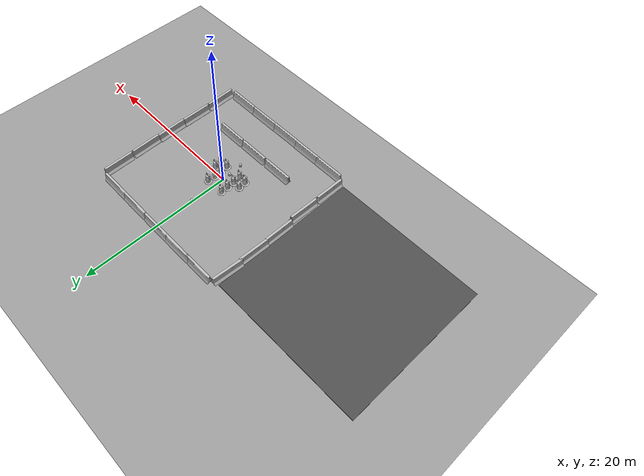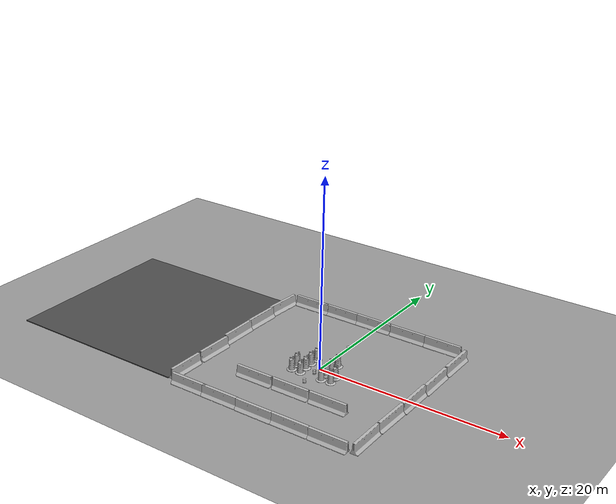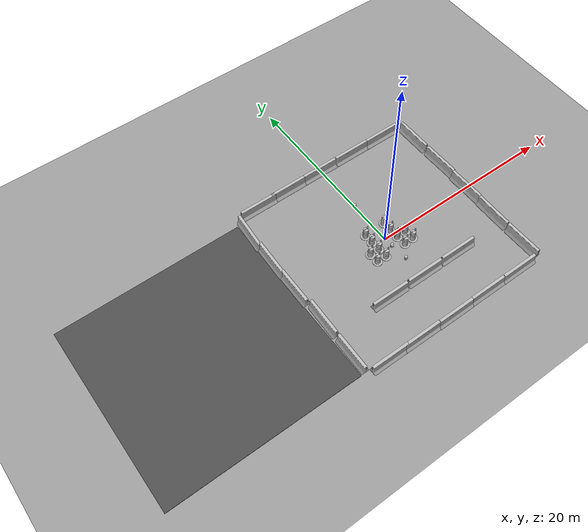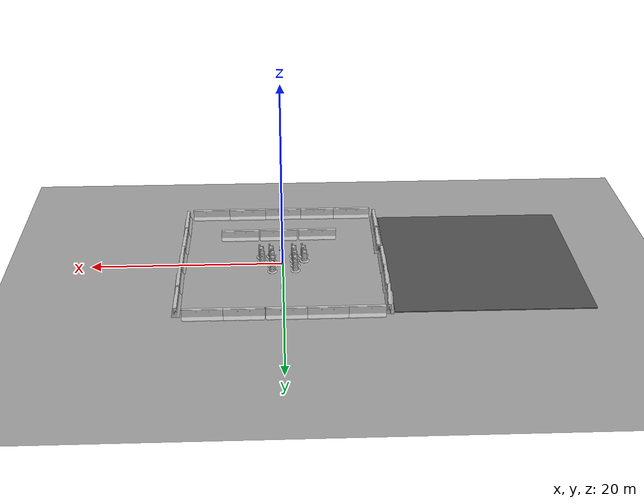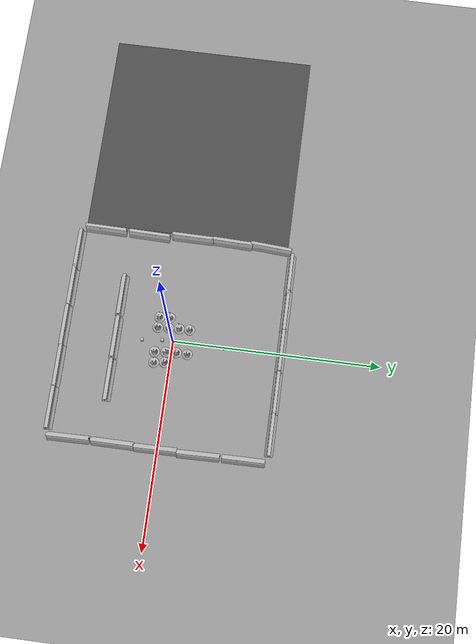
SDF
<sdf version="1.4">
 <world name="default">
  <light name="sun" type="directional">
   <pose>0 0 10 0 -0 0</pose>
   <diffuse>0.8 0.8 0.8 1</diffuse>
   <specular>0.2 0.2 0.2 1</specular>
   <attenuation>
    <range>1000</range>
    <constant>0.9</constant>
    <linear>0.01</linear>
    <quadratic>0.001</quadratic>
   </attenuation>
   <direction>-0.5 0.1 -0.9</direction>
  </light>
  <physics type="ode">
   <max_step_size>0.01</max_step_size>
   <real_time_factor>1</real_time_factor>
   <real_time_update_rate>100</real_time_update_rate>
   <gravity>0 0 -9.8</gravity>
  </physics>
  <scene><ambient>0.4 0.4 0.4 1</ambient><background>0.7 0.7 0.7 1</background><shadows>1</shadows></scene>
  <spherical_coordinates>
   <surface_model>EARTH_WGS84</surface_model>
   <latitude_deg>0</latitude_deg>
   <longitude_deg>0</longitude_deg>
   <elevation>0</elevation>
   <heading_deg>0</heading_deg>
  </spherical_coordinates>
  <model name="mobile_base">
   <link name="base_footprint">
    <inertial>
     <pose>-0.00949586 1.25983e-05 0.135573 0 -0 0</pose>
     <mass>4.9213</mass>
     <inertia>
      <ixx>0.142129</ixx>
      <ixy>-4.09257e-06</ixy>
      <ixz>0.0154899</ixz>
      <iyy>0.140784</iyy>
      <iyz>6.52071e-06</iyz>
      <izz>0.0801071</izz>
     </inertia>
    </inertial>
    <collision name="base_footprint_collision_base_link">
     <pose>0 0 0.06969 0 -0 0</pose>
     <geometry><cylinder><length>0.10938</length><radius>0.178</radius></cylinder></geometry>
     <surface><friction><ode><mu>0.3</mu><mu2>0.3</mu2></ode></friction></surface>
    </collision>
    <collision name="base_footprint_collision_camera_link">
     <pose>-0.118 0 0.2812 0 -0 0</pose>
     <geometry><box><size>0.07271 0.27794 0.073</size></box></geometry>
    </collision>
    <collision name="base_footprint_collision_caster_back_link">
     <pose>-0.135 0 0.0192 -1.5708 0 0</pose>
     <geometry><cylinder><length>0.0176</length><radius>0.017</radius></cylinder></geometry>
     <surface>
      <contact><ode><kp>1e+06</kp><kd>100</kd><max_vel>1</max_vel><min_depth>0.001</min_depth></ode></contact>
      <friction><ode><mu>0</mu><mu2>0</mu2></ode></friction>
     </surface>
    </collision>
    <collision name="base_footprint_collision_caster_front_link">
     <pose>0.115 0 0.0172 -1.5708 0 0</pose>
     <geometry><cylinder><length>0.0176</length><radius>0.017</radius></cylinder></geometry>
     <surface>
      <contact><ode><kp>1e+06</kp><kd>100</kd><max_vel>1</max_vel><min_depth>0.001</min_depth></ode></contact>
      <friction><ode><mu>0</mu><mu2>0</mu2></ode></friction>
     </surface>
    </collision>
    <collision name="base_footprint_collision_plate_bottom_link">
     <pose>0 0 0.1408 0 -0 0</pose>
     <geometry><cylinder><length>0.006</length><radius>0.17</radius></cylinder></geometry>
    </collision>
    <collision name="base_footprint_collision_plate_middle_link">
     <pose>0 0 0.1976 0 -0 0</pose>
     <geometry><cylinder><length>0.006</length><radius>0.17</radius></cylinder></geometry>
    </collision>
    <collision name="base_footprint_collision_plate_top_link">
     <pose>0 0 0.4068 0 -0 0</pose>
     <geometry><cylinder><length>0.006</length><radius>0.17</radius></cylinder></geometry>
    </collision>
    <collision name="base_footprint_collision_pole_bottom_0_link">
     <pose>0.12 0.082 0.113 0 -0 0</pose>
     <geometry><cylinder><length>0.0492</length><radius>0.006</radius></cylinder></geometry>
    </collision>
    <collision name="base_footprint_collision_pole_bottom_1_link">
     <pose>0.055 0.12 0.113 0 -0 0</pose>
     <geometry><cylinder><length>0.0492</length><radius>0.006</radius></cylinder></geometry>
    </collision>
    <collision name="base_footprint_collision_pole_bottom_2_link">
     <pose>-0.055 0.12 0.113 0 -0 0</pose>
     <geometry><cylinder><length>0.0492</length><radius>0.006</radius></cylinder></geometry>
    </collision>
    <collision name="base_footprint_collision_pole_bottom_3_link">
     <pose>0.12 -0.082 0.113 0 -0 0</pose>
     <geometry><cylinder><length>0.0492</length><radius>0.006</radius></cylinder></geometry>
    </collision>
    <collision name="base_footprint_collision_pole_bottom_4_link">
     <pose>0.055 -0.12 0.113 0 -0 0</pose>
     <geometry><cylinder><length>0.0492</length><radius>0.006</radius></cylinder></geometry>
    </collision>
    <collision name="base_footprint_collision_pole_bottom_5_link">
     <pose>-0.055 -0.12 0.113 0 -0 0</pose>
     <geometry><cylinder><length>0.0492</length><radius>0.006</radius></cylinder></geometry>
    </collision>
    <collision name="base_footprint_collision_pole_kinect_0_link">
     <pose>-0.1024 0.098 0.2474 0 -0 0</pose>
     <geometry><cylinder><length>0.0936</length><radius>0.006</radius></cylinder></geometry>
    </collision>
    <collision name="base_footprint_collision_pole_kinect_1_link">
     <pose>-0.1024 -0.098 0.2474 0 -0 0</pose>
     <geometry><cylinder><length>0.0936</length><radius>0.006</radius></cylinder></geometry>
    </collision>
    <collision name="base_footprint_collision_pole_middle_0_link">
     <pose>0.0381 0.1505 0.1742 0 -0 0</pose>
     <geometry><cylinder><length>0.0608</length><radius>0.006</radius></cylinder></geometry>
    </collision>
    <collision name="base_footprint_collision_pole_middle_1_link">
     <pose>0.0381 -0.1505 0.1742 0 -0 0</pose>
     <geometry><cylinder><length>0.0608</length><radius>0.006</radius></cylinder></geometry>
    </collision>
    <collision name="base_footprint_collision_pole_middle_2_link">
     <pose>-0.0381 0.1505 0.1742 0 -0 0</pose>
     <geometry><cylinder><length>0.0608</length><radius>0.006</radius></cylinder></geometry>
    </collision>
    <collision name="base_footprint_collision_pole_middle_3_link">
     <pose>-0.0381 -0.1505 0.1742 0 -0 0</pose>
     <geometry><cylinder><length>0.0608</length><radius>0.006</radius></cylinder></geometry>
    </collision>
    <collision name="base_footprint_collision_pole_top_0_link">
     <pose>0.0381 0.1505 0.3022 0 -0 0</pose>
     <geometry><cylinder><length>0.2032</length><radius>0.006</radius></cylinder></geometry>
    </collision>
    <collision name="base_footprint_collision_pole_top_1_link">
     <pose>0.0381 -0.1505 0.3022 0 -0 0</pose>
     <geometry><cylinder><length>0.2032</length><radius>0.006</radius></cylinder></geometry>
    </collision>
    <collision name="base_footprint_collision_pole_top_2_link">
     <pose>-0.0381 0.1505 0.3022 0 -0 0</pose>
     <geometry><cylinder><length>0.2032</length><radius>0.006</radius></cylinder></geometry>
    </collision>
    <collision name="base_footprint_collision_pole_top_3_link">
     <pose>-0.0381 -0.1505 0.3022 0 -0 0</pose>
     <geometry><cylinder><length>0.2032</length><radius>0.006</radius></cylinder></geometry>
    </collision>
    <visual name="base_footprint_visual_base_link">
     <pose>0.001 0 0.06219 0 -0 0</pose>
     <geometry>
      <mesh><scale>1 1 1</scale><uri>/opt/ros/indigo/share/kobuki_description/meshes/main_body.dae</uri></mesh>
     </geometry>
    </visual>
    <visual name="base_footprint_visual_camera_link">
     <pose>-0.118 0 0.2812 0 -0 1.5708</pose>
     <geometry>
      <mesh>
       <scale>1 1 1</scale>
       <uri>/opt/ros/indigo/share/turtlebot_description/meshes/sensors/kinect.dae</uri>
      </mesh>
     </geometry>
    </visual>
    <visual name="base_footprint_visual_plate_bottom_link">
     <pose>0.02364 0 0.1408 0 -0 0</pose>
     <geometry>
      <mesh>
       <scale>1 1 1</scale>
       <uri>/opt/ros/indigo/share/turtlebot_description/meshes/stacks/hexagons/plate_bottom.dae</uri>
      </mesh>
     </geometry>
    </visual>
    <visual name="base_footprint_visual_plate_middle_link">
     <pose>-0.01364 0 0.1976 0 -0 0</pose>
     <geometry>
      <mesh>
       <scale>1 1 1</scale>
       <uri>/opt/ros/indigo/share/turtlebot_description/meshes/stacks/hexagons/plate_middle.dae</uri>
      </mesh>
     </geometry>
    </visual>
    <visual name="base_footprint_visual_plate_top_link">
     <pose>-0.01364 0 0.4068 0 -0 0</pose>
     <geometry>
      <mesh>
       <scale>1 1 1</scale>
       <uri>/opt/ros/indigo/share/turtlebot_description/meshes/stacks/hexagons/plate_top.dae</uri>
      </mesh>
     </geometry>
    </visual>
    <visual name="base_footprint_visual_pole_bottom_0_link">
     <pose>0.12 0.082 0.113 0 -0 0</pose>
     <geometry>
      <mesh>
       <scale>1 1 1</scale>
       <uri>/opt/ros/indigo/share/turtlebot_description/meshes/stacks/hexagons/pole_bottom.dae</uri>
      </mesh>
     </geometry>
    </visual>
    <visual name="base_footprint_visual_pole_bottom_1_link">
     <pose>0.055 0.12 0.113 0 -0 0</pose>
     <geometry>
      <mesh>
       <scale>1 1 1</scale>
       <uri>/opt/ros/indigo/share/turtlebot_description/meshes/stacks/hexagons/pole_bottom.dae</uri>
      </mesh>
     </geometry>
    </visual>
    <visual name="base_footprint_visual_pole_bottom_2_link">
     <pose>-0.055 0.12 0.113 0 -0 0</pose>
     <geometry>
      <mesh>
       <scale>1 1 1</scale>
       <uri>/opt/ros/indigo/share/turtlebot_description/meshes/stacks/hexagons/pole_bottom.dae</uri>
      </mesh>
     </geometry>
    </visual>
    <visual name="base_footprint_visual_pole_bottom_3_link">
     <pose>0.12 -0.082 0.113 0 -0 0</pose>
     <geometry>
      <mesh>
       <scale>1 1 1</scale>
       <uri>/opt/ros/indigo/share/turtlebot_description/meshes/stacks/hexagons/pole_bottom.dae</uri>
      </mesh>
     </geometry>
    </visual>
    <visual name="base_footprint_visual_pole_bottom_4_link">
     <pose>0.055 -0.12 0.113 0 -0 0</pose>
     <geometry>
      <mesh>
       <scale>1 1 1</scale>
       <uri>/opt/ros/indigo/share/turtlebot_description/meshes/stacks/hexagons/pole_bottom.dae</uri>
      </mesh>
     </geometry>
    </visual>
    <visual name="base_footprint_visual_pole_bottom_5_link">
     <pose>-0.055 -0.12 0.113 0 -0 0</pose>
     <geometry>
      <mesh>
       <scale>1 1 1</scale>
       <uri>/opt/ros/indigo/share/turtlebot_description/meshes/stacks/hexagons/pole_bottom.dae</uri>
      </mesh>
     </geometry>
    </visual>
    <visual name="base_footprint_visual_pole_kinect_0_link">
     <pose>-0.1024 0.098 0.2374 0 -0 0</pose>
     <geometry>
      <mesh>
       <scale>1 1 1</scale>
       <uri>/opt/ros/indigo/share/turtlebot_description/meshes/sensors/sensor_pole.dae</uri>
      </mesh>
     </geometry>
    </visual>
    <visual name="base_footprint_visual_pole_kinect_1_link">
     <pose>-0.1024 -0.098 0.2374 0 -0 0</pose>
     <geometry>
      <mesh>
       <scale>1 1 1</scale>
       <uri>/opt/ros/indigo/share/turtlebot_description/meshes/sensors/sensor_pole.dae</uri>
      </mesh>
     </geometry>
    </visual>
    <visual name="base_footprint_visual_pole_middle_0_link">
     <pose>0.0381 0.1505 0.1742 3.14159 -2.06823e-13 3.14159</pose>
     <geometry>
      <mesh>
       <scale>1 1 1</scale>
       <uri>/opt/ros/indigo/share/turtlebot_description/meshes/stacks/hexagons/pole_middle.dae</uri>
      </mesh>
     </geometry>
    </visual>
    <visual name="base_footprint_visual_pole_middle_1_link">
     <pose>0.0381 -0.1505 0.1742 3.14159 -2.06823e-13 3.14159</pose>
     <geometry>
      <mesh>
       <scale>1 1 1</scale>
       <uri>/opt/ros/indigo/share/turtlebot_description/meshes/stacks/hexagons/pole_middle.dae</uri>
      </mesh>
     </geometry>
    </visual>
    <visual name="base_footprint_visual_pole_middle_2_link">
     <pose>-0.0381 0.1505 0.1742 3.14159 -2.06823e-13 3.14159</pose>
     <geometry>
      <mesh>
       <scale>1 1 1</scale>
       <uri>/opt/ros/indigo/share/turtlebot_description/meshes/stacks/hexagons/pole_middle.dae</uri>
      </mesh>
     </geometry>
    </visual>
    <visual name="base_footprint_visual_pole_middle_3_link">
     <pose>-0.0381 -0.1505 0.1742 3.14159 -2.06823e-13 3.14159</pose>
     <geometry>
      <mesh>
       <scale>1 1 1</scale>
       <uri>/opt/ros/indigo/share/turtlebot_description/meshes/stacks/hexagons/pole_middle.dae</uri>
      </mesh>
     </geometry>
    </visual>
    <visual name="base_footprint_visual_pole_top_0_link">
     <pose>0.0381 0.1505 0.3022 0 -0 0</pose>
     <geometry>
      <mesh>
       <scale>1 1 1</scale>
       <uri>/opt/ros/indigo/share/turtlebot_description/meshes/stacks/hexagons/pole_top.dae</uri>
      </mesh>
     </geometry>
    </visual>
    <visual name="base_footprint_visual_pole_top_1_link">
     <pose>0.0381 -0.1505 0.3022 0 -0 0</pose>
     <geometry>
      <mesh>
       <scale>1 1 1</scale>
       <uri>/opt/ros/indigo/share/turtlebot_description/meshes/stacks/hexagons/pole_top.dae</uri>
      </mesh>
     </geometry>
    </visual>
    <visual name="base_footprint_visual_pole_top_2_link">
     <pose>-0.0381 0.1505 0.3022 0 -0 0</pose>
     <geometry>
      <mesh>
       <scale>1 1 1</scale>
       <uri>/opt/ros/indigo/share/turtlebot_description/meshes/stacks/hexagons/pole_top.dae</uri>
      </mesh>
     </geometry>
    </visual>
    <visual name="base_footprint_visual_pole_top_3_link">
     <pose>-0.0381 -0.1505 0.3022 0 -0 0</pose>
     <geometry>
      <mesh>
       <scale>1 1 1</scale>
       <uri>/opt/ros/indigo/share/turtlebot_description/meshes/stacks/hexagons/pole_top.dae</uri>
      </mesh>
     </geometry>
    </visual>
    <velocity_decay><linear>0</linear><angular>0</angular></velocity_decay>
    <sensor name="bumpers" type="contact">
     <always_on>1</always_on>
     <update_rate>50</update_rate>
     <visualize>1</visualize>
     <contact><collision>base_footprint_collision_base_link</collision><topic>__default_topic__</topic></contact>
     <pose>0 0 0.0102 0 -0 0</pose>
    </sensor>
    <velocity_decay><linear>0</linear><angular>0</angular></velocity_decay>
    <sensor name="camera" type="depth">
     <always_on>1</always_on>
     <update_rate>20</update_rate>
     <camera name="__default__">
      <horizontal_fov>1.0472</horizontal_fov>
      <image><format>R8G8B8</format><width>640</width><height>480</height></image>
      <clip><near>0.05</near><far>8</far></clip>
     </camera>
     <plugin name="kinect_camera_controller" filename="libgazebo_ros_openni_kinect.so">
      <cameraName>camera</cameraName>
      <alwaysOn>true</alwaysOn>
      <updateRate>10</updateRate>
      <imageTopicName>rgb/image_raw</imageTopicName>
      <depthImageTopicName>depth/image_raw</depthImageTopicName>
      <pointCloudTopicName>depth/points</pointCloudTopicName>
      <cameraInfoTopicName>rgb/camera_info</cameraInfoTopicName>
      <depthImageCameraInfoTopicName>depth/camera_info</depthImageCameraInfoTopicName>
      <frameName>camera_depth_optical_frame</frameName>
      <baseline>0.1</baseline>
      <distortion_k1>0.0</distortion_k1>
      <distortion_k2>0.0</distortion_k2>
      <distortion_k3>0.0</distortion_k3>
      <distortion_t1>0.0</distortion_t1>
      <distortion_t2>0.0</distortion_t2>
      <pointCloudCutoff>0.4</pointCloudCutoff>
      <robotNamespace>/</robotNamespace>
     </plugin>
     <pose>-0.118 0 0.2812 0 -0 0</pose>
    </sensor>
    <velocity_decay><linear>0</linear><angular>0</angular></velocity_decay>
    <velocity_decay><linear>0</linear><angular>0</angular></velocity_decay>
    <velocity_decay><linear>0</linear><angular>0</angular></velocity_decay>
    <sensor name="cliff_sensor_front" type="ray">
     <always_on>1</always_on>
     <update_rate>50</update_rate>
     <visualize>1</visualize>
     <ray>
      <scan>
       <horizontal>
        <samples>50</samples>
        <resolution>1</resolution>
        <min_angle>-0.0436</min_angle>
        <max_angle>0.0436</max_angle>
       </horizontal>
      </scan>
      <range><min>0.01</min><max>0.15</max><resolution>1</resolution></range>
     </ray>
     <pose>0.156 0 0.0316 3.14159 1.57079 3.14159</pose>
    </sensor>
    <velocity_decay><linear>0</linear><angular>0</angular></velocity_decay>
    <sensor name="cliff_sensor_left" type="ray">
     <always_on>1</always_on>
     <update_rate>50</update_rate>
     <visualize>1</visualize>
     <ray>
      <scan>
       <horizontal>
        <samples>50</samples>
        <resolution>1</resolution>
        <min_angle>-0.0436</min_angle>
        <max_angle>0.0436</max_angle>
       </horizontal>
      </scan>
      <range><min>0.01</min><max>0.15</max><resolution>1</resolution></range>
     </ray>
     <pose>0.08734 0.13601 0.0316 3.14159 1.57079 3.14159</pose>
    </sensor>
    <velocity_decay><linear>0</linear><angular>0</angular></velocity_decay>
    <sensor name="cliff_sensor_right" type="ray">
     <always_on>1</always_on>
     <update_rate>50</update_rate>
     <visualize>1</visualize>
     <ray>
      <scan>
       <horizontal>
        <samples>50</samples>
        <resolution>1</resolution>
        <min_angle>-0.0436</min_angle>
        <max_angle>0.0436</max_angle>
       </horizontal>
      </scan>
      <range><min>0.01</min><max>0.15</max><resolution>1</resolution></range>
     </ray>
     <pose>0.085 -0.13601 0.0316 3.14159 1.57079 3.14159</pose>
    </sensor>
    <velocity_decay><linear>0</linear><angular>0</angular></velocity_decay>
    <sensor name="imu" type="imu">
     <always_on>1</always_on>
     <update_rate>50</update_rate>
     <visualize>0</visualize>
     <imu>
      <noise>
       <type>gaussian</type>
       <rate><mean>0</mean><stddev>1.96e-06</stddev><bias_mean>0</bias_mean><bias_stddev>0</bias_stddev></rate>
       <accel><mean>0</mean><stddev>0.017</stddev><bias_mean>0.1</bias_mean><bias_stddev>0.001</bias_stddev></accel>
      </noise>
     </imu>
     <pose>0.056 0.062 0.0304 0 -0 0</pose>
    </sensor>
   </link>
   <link name="wheel_left_link">
    <pose>0 0.115 0.0352 -1.5708 0 0</pose>
    <inertial>
     <mass>0.01</mass>
     <inertia><ixx>0.001</ixx><ixy>0</ixy><ixz>0</ixz><iyy>0.001</iyy><iyz>0</iyz><izz>0.001</izz></inertia>
    </inertial>
    <collision name="wheel_left_link_collision">
     <geometry><cylinder><length>0.0206</length><radius>0.0352</radius></cylinder></geometry>
     <surface>
      <contact><ode><kp>1e+06</kp><kd>100</kd><max_vel>1</max_vel><min_depth>0.001</min_depth></ode></contact>
      <friction><ode><mu>1</mu><mu2>1</mu2></ode></friction>
     </surface>
    </collision>
    <visual name="wheel_left_link_visual">
     <geometry>
      <mesh><scale>1 1 1</scale><uri>/opt/ros/indigo/share/kobuki_description/meshes/wheel.dae</uri></mesh>
     </geometry>
    </visual>
    <velocity_decay><linear>0</linear><angular>0</angular></velocity_decay>
   </link>
   <joint name="wheel_left_joint" type="revolute">
    <child>wheel_left_link</child>
    <parent>base_footprint</parent>
    <axis><xyz>0 1 0</xyz><limit><lower>-1e+16</lower><upper>1e+16</upper></limit></axis>
   </joint>
   <link name="wheel_right_link">
    <pose>0 -0.115 0.0352 -1.5708 0 0</pose>
    <inertial>
     <mass>0.01</mass>
     <inertia><ixx>0.001</ixx><ixy>0</ixy><ixz>0</ixz><iyy>0.001</iyy><iyz>0</iyz><izz>0.001</izz></inertia>
    </inertial>
    <collision name="wheel_right_link_collision">
     <geometry><cylinder><length>0.0206</length><radius>0.035</radius></cylinder></geometry>
     <surface>
      <contact><ode><kp>1e+06</kp><kd>100</kd><max_vel>1</max_vel><min_depth>0.001</min_depth></ode></contact>
      <friction><ode><mu>1</mu><mu2>1</mu2></ode></friction>
     </surface>
    </collision>
    <visual name="wheel_right_link_visual">
     <geometry>
      <mesh><scale>1 1 1</scale><uri>/opt/ros/indigo/share/kobuki_description/meshes/wheel.dae</uri></mesh>
     </geometry>
    </visual>
    <velocity_decay><linear>0</linear><angular>0</angular></velocity_decay>
   </link>
   <joint name="wheel_right_joint" type="revolute">
    <child>wheel_right_link</child>
    <parent>base_footprint</parent>
    <axis><xyz>0 1 0</xyz><limit><lower>-1e+16</lower><upper>1e+16</upper></limit></axis>
   </joint>
   <static>0</static>
   <plugin name="kobuki_controller" filename="libgazebo_ros_kobuki.so">
    <publish_tf>1</publish_tf>
    <left_wheel_joint_name>wheel_left_joint</left_wheel_joint_name>
    <right_wheel_joint_name>wheel_right_joint</right_wheel_joint_name>
    <wheel_separation>.230</wheel_separation>
    <wheel_diameter>0.070</wheel_diameter>
    <torque>1.0</torque>
    <velocity_command_timeout>0.6</velocity_command_timeout>
    <cliff_sensor_left_name>cliff_sensor_left</cliff_sensor_left_name>
    <cliff_sensor_center_name>cliff_sensor_front</cliff_sensor_center_name>
    <cliff_sensor_right_name>cliff_sensor_right</cliff_sensor_right_name>
    <cliff_detection_threshold>0.04</cliff_detection_threshold>
    <bumper_name>bumpers</bumper_name>
    <imu_name>imu</imu_name>
    <robotNamespace>/</robotNamespace>
   </plugin>
   <pose>0.037756 -1.03166 -0.001131 4.1e-05 -0.008002 -1.65563</pose>
  </model>
  <light name="sun" type="directional">
   <pose>18 -17 10 0 -0 0</pose>
   <diffuse>0.8 0.8 0.8 1</diffuse>
   <specular>0.2 0.2 0.2 1</specular>
   <attenuation>
    <range>1000</range>
    <constant>0.9</constant>
    <linear>0.01</linear>
    <quadratic>0.001</quadratic>
   </attenuation>
   <direction>-0.5 0.1 -0.9</direction>
  </light>
  <model name="asphalt_plane">
   <static>1</static>
   <link name="link">
    <collision name="collision"><geometry><box><size>20 20 0.1</size></box></geometry></collision>
    <visual name="visual">
     <cast_shadows>0</cast_shadows>
     <geometry><box><size>20 20 0.1</size></box></geometry>
     <material>
      <script>
       <uri>model://asphalt_plane/materials/scripts</uri>
       <uri>model://asphalt_plane/materials/textures</uri>
       <name>vrc/asphalt</name>
      </script>
     </material>
    </visual>
    <velocity_decay><linear>0</linear><angular>0</angular></velocity_decay>
   </link>
   <pose>-20.8561 -0.082108 0 0 -0 0</pose>
  </model>
  <model name="ground_plane_0">
   <static>1</static>
   <link name="link">
    <collision name="collision">
     <geometry><plane><normal>0 0 1</normal><size>100 100</size></plane></geometry>
     <surface><friction><ode><mu>100</mu><mu2>50</mu2></ode></friction></surface>
    </collision>
    <visual name="visual">
     <cast_shadows>0</cast_shadows>
     <geometry><plane><normal>0 0 1</normal><size>100 100</size></plane></geometry>
     <material>
      <script><uri>file://media/materials/scripts/gazebo.material</uri><name>Gazebo/Grey</name></script>
     </material>
    </visual>
    <velocity_decay><linear>0</linear><angular>0</angular></velocity_decay>
   </link>
   <pose>-12 -1 0 0 -0 0</pose>
  </model>
  <model name="jersey_barrier">
   <static>1</static>
   <link name="link">
    <visual name="visual">
     <geometry><mesh><uri>model://jersey_barrier/meshes/jersey_barrier.dae</uri></mesh></geometry>
    </visual>
    <collision name="upright">
     <pose>0 0 0.5715 0 -0 0</pose>
     <geometry><box><size>4.06542 0.3063 1.143</size></box></geometry>
    </collision>
    <collision name="base">
     <pose>0 0 0.032258 0 -0 0</pose>
     <geometry><box><size>4.06542 0.8107 0.064516</size></box></geometry>
    </collision>
    <collision name="base2">
     <pose>0 0 0.1 0 -0 0</pose>
     <geometry><box><size>4.06542 0.65 0.1</size></box></geometry>
    </collision>
    <collision name="base3">
     <pose>0 0 0.2 0 -0 0</pose>
     <geometry><box><size>4.06542 0.5 0.1</size></box></geometry>
    </collision>
    <collision name="left-angle">
     <pose>0 -0.224 0.2401 0.9 -0 0</pose>
     <geometry><box><size>4.06542 0.5 0.064516</size></box></geometry>
    </collision>
    <collision name="right-angle">
     <pose>0 0.224 0.2401 -0.9 0 0</pose>
     <geometry><box><size>4.06542 0.5 0.064516</size></box></geometry>
    </collision>
    <velocity_decay><linear>0</linear><angular>0</angular></velocity_decay>
   </link>
   <pose>-0.151426 -10.4913 0 0 -0 0</pose>
  </model>
  <model name="jersey_barrier_0">
   <static>1</static>
   <link name="link">
    <visual name="visual">
     <geometry><mesh><uri>model://jersey_barrier/meshes/jersey_barrier.dae</uri></mesh></geometry>
    </visual>
    <collision name="upright">
     <pose>0 0 0.5715 0 -0 0</pose>
     <geometry><box><size>4.06542 0.3063 1.143</size></box></geometry>
    </collision>
    <collision name="base">
     <pose>0 0 0.032258 0 -0 0</pose>
     <geometry><box><size>4.06542 0.8107 0.064516</size></box></geometry>
    </collision>
    <collision name="base2">
     <pose>0 0 0.1 0 -0 0</pose>
     <geometry><box><size>4.06542 0.65 0.1</size></box></geometry>
    </collision>
    <collision name="base3">
     <pose>0 0 0.2 0 -0 0</pose>
     <geometry><box><size>4.06542 0.5 0.1</size></box></geometry>
    </collision>
    <collision name="left-angle">
     <pose>0 -0.224 0.2401 0.9 -0 0</pose>
     <geometry><box><size>4.06542 0.5 0.064516</size></box></geometry>
    </collision>
    <collision name="right-angle">
     <pose>0 0.224 0.2401 -0.9 0 0</pose>
     <geometry><box><size>4.06542 0.5 0.064516</size></box></geometry>
    </collision>
    <velocity_decay><linear>0</linear><angular>0</angular></velocity_decay>
   </link>
   <pose>-7.87258 -10.4328 0 0 -0 0</pose>
  </model>
  <model name="jersey_barrier_1">
   <static>1</static>
   <link name="link">
    <visual name="visual">
     <geometry><mesh><uri>model://jersey_barrier/meshes/jersey_barrier.dae</uri></mesh></geometry>
    </visual>
    <collision name="upright">
     <pose>0 0 0.5715 0 -0 0</pose>
     <geometry><box><size>4.06542 0.3063 1.143</size></box></geometry>
    </collision>
    <collision name="base">
     <pose>0 0 0.032258 0 -0 0</pose>
     <geometry><box><size>4.06542 0.8107 0.064516</size></box></geometry>
    </collision>
    <collision name="base2">
     <pose>0 0 0.1 0 -0 0</pose>
     <geometry><box><size>4.06542 0.65 0.1</size></box></geometry>
    </collision>
    <collision name="base3">
     <pose>0 0 0.2 0 -0 0</pose>
     <geometry><box><size>4.06542 0.5 0.1</size></box></geometry>
    </collision>
    <collision name="left-angle">
     <pose>0 -0.224 0.2401 0.9 -0 0</pose>
     <geometry><box><size>4.06542 0.5 0.064516</size></box></geometry>
    </collision>
    <collision name="right-angle">
     <pose>0 0.224 0.2401 -0.9 0 0</pose>
     <geometry><box><size>4.06542 0.5 0.064516</size></box></geometry>
    </collision>
    <velocity_decay><linear>0</linear><angular>0</angular></velocity_decay>
   </link>
   <pose>-4.18041 -10.4529 0 0 -0 0</pose>
  </model>
  <model name="jersey_barrier_2">
   <static>1</static>
   <link name="link">
    <visual name="visual">
     <geometry><mesh><uri>model://jersey_barrier/meshes/jersey_barrier.dae</uri></mesh></geometry>
    </visual>
    <collision name="upright">
     <pose>0 0 0.5715 0 -0 0</pose>
     <geometry><box><size>4.06542 0.3063 1.143</size></box></geometry>
    </collision>
    <collision name="base">
     <pose>0 0 0.032258 0 -0 0</pose>
     <geometry><box><size>4.06542 0.8107 0.064516</size></box></geometry>
    </collision>
    <collision name="base2">
     <pose>0 0 0.1 0 -0 0</pose>
     <geometry><box><size>4.06542 0.65 0.1</size></box></geometry>
    </collision>
    <collision name="base3">
     <pose>0 0 0.2 0 -0 0</pose>
     <geometry><box><size>4.06542 0.5 0.1</size></box></geometry>
    </collision>
    <collision name="left-angle">
     <pose>0 -0.224 0.2401 0.9 -0 0</pose>
     <geometry><box><size>4.06542 0.5 0.064516</size></box></geometry>
    </collision>
    <collision name="right-angle">
     <pose>0 0.224 0.2401 -0.9 0 0</pose>
     <geometry><box><size>4.06542 0.5 0.064516</size></box></geometry>
    </collision>
    <velocity_decay><linear>0</linear><angular>0</angular></velocity_decay>
   </link>
   <pose>7.90162 -10.4784 0 0 -0 0</pose>
  </model>
  <model name="jersey_barrier_3">
   <static>1</static>
   <link name="link">
    <visual name="visual">
     <geometry><mesh><uri>model://jersey_barrier/meshes/jersey_barrier.dae</uri></mesh></geometry>
    </visual>
    <collision name="upright">
     <pose>0 0 0.5715 0 -0 0</pose>
     <geometry><box><size>4.06542 0.3063 1.143</size></box></geometry>
    </collision>
    <collision name="base">
     <pose>0 0 0.032258 0 -0 0</pose>
     <geometry><box><size>4.06542 0.8107 0.064516</size></box></geometry>
    </collision>
    <collision name="base2">
     <pose>0 0 0.1 0 -0 0</pose>
     <geometry><box><size>4.06542 0.65 0.1</size></box></geometry>
    </collision>
    <collision name="base3">
     <pose>0 0 0.2 0 -0 0</pose>
     <geometry><box><size>4.06542 0.5 0.1</size></box></geometry>
    </collision>
    <collision name="left-angle">
     <pose>0 -0.224 0.2401 0.9 -0 0</pose>
     <geometry><box><size>4.06542 0.5 0.064516</size></box></geometry>
    </collision>
    <collision name="right-angle">
     <pose>0 0.224 0.2401 -0.9 0 0</pose>
     <geometry><box><size>4.06542 0.5 0.064516</size></box></geometry>
    </collision>
    <velocity_decay><linear>0</linear><angular>0</angular></velocity_decay>
   </link>
   <pose>3.84037 -10.4642 0 0 -0 0</pose>
  </model>
  <model name="jersey_barrier_4">
   <static>1</static>
   <link name="link">
    <visual name="visual">
     <geometry><mesh><uri>model://jersey_barrier/meshes/jersey_barrier.dae</uri></mesh></geometry>
    </visual>
    <collision name="upright">
     <pose>0 0 0.5715 0 -0 0</pose>
     <geometry><box><size>4.06542 0.3063 1.143</size></box></geometry>
    </collision>
    <collision name="base">
     <pose>0 0 0.032258 0 -0 0</pose>
     <geometry><box><size>4.06542 0.8107 0.064516</size></box></geometry>
    </collision>
    <collision name="base2">
     <pose>0 0 0.1 0 -0 0</pose>
     <geometry><box><size>4.06542 0.65 0.1</size></box></geometry>
    </collision>
    <collision name="base3">
     <pose>0 0 0.2 0 -0 0</pose>
     <geometry><box><size>4.06542 0.5 0.1</size></box></geometry>
    </collision>
    <collision name="left-angle">
     <pose>0 -0.224 0.2401 0.9 -0 0</pose>
     <geometry><box><size>4.06542 0.5 0.064516</size></box></geometry>
    </collision>
    <collision name="right-angle">
     <pose>0 0.224 0.2401 -0.9 0 0</pose>
     <geometry><box><size>4.06542 0.5 0.064516</size></box></geometry>
    </collision>
    <velocity_decay><linear>0</linear><angular>0</angular></velocity_decay>
   </link>
   <pose>3.84438 10.4465 0 0 -0 0</pose>
  </model>
  <model name="jersey_barrier_5">
   <static>1</static>
   <link name="link">
    <visual name="visual">
     <geometry><mesh><uri>model://jersey_barrier/meshes/jersey_barrier.dae</uri></mesh></geometry>
    </visual>
    <collision name="upright">
     <pose>0 0 0.5715 0 -0 0</pose>
     <geometry><box><size>4.06542 0.3063 1.143</size></box></geometry>
    </collision>
    <collision name="base">
     <pose>0 0 0.032258 0 -0 0</pose>
     <geometry><box><size>4.06542 0.8107 0.064516</size></box></geometry>
    </collision>
    <collision name="base2">
     <pose>0 0 0.1 0 -0 0</pose>
     <geometry><box><size>4.06542 0.65 0.1</size></box></geometry>
    </collision>
    <collision name="base3">
     <pose>0 0 0.2 0 -0 0</pose>
     <geometry><box><size>4.06542 0.5 0.1</size></box></geometry>
    </collision>
    <collision name="left-angle">
     <pose>0 -0.224 0.2401 0.9 -0 0</pose>
     <geometry><box><size>4.06542 0.5 0.064516</size></box></geometry>
    </collision>
    <collision name="right-angle">
     <pose>0 0.224 0.2401 -0.9 0 0</pose>
     <geometry><box><size>4.06542 0.5 0.064516</size></box></geometry>
    </collision>
    <velocity_decay><linear>0</linear><angular>0</angular></velocity_decay>
   </link>
   <pose>-4.26904 10.4439 0 0 -0 0</pose>
  </model>
  <model name="jersey_barrier_6">
   <static>1</static>
   <link name="link">
    <visual name="visual">
     <geometry><mesh><uri>model://jersey_barrier/meshes/jersey_barrier.dae</uri></mesh></geometry>
    </visual>
    <collision name="upright">
     <pose>0 0 0.5715 0 -0 0</pose>
     <geometry><box><size>4.06542 0.3063 1.143</size></box></geometry>
    </collision>
    <collision name="base">
     <pose>0 0 0.032258 0 -0 0</pose>
     <geometry><box><size>4.06542 0.8107 0.064516</size></box></geometry>
    </collision>
    <collision name="base2">
     <pose>0 0 0.1 0 -0 0</pose>
     <geometry><box><size>4.06542 0.65 0.1</size></box></geometry>
    </collision>
    <collision name="base3">
     <pose>0 0 0.2 0 -0 0</pose>
     <geometry><box><size>4.06542 0.5 0.1</size></box></geometry>
    </collision>
    <collision name="left-angle">
     <pose>0 -0.224 0.2401 0.9 -0 0</pose>
     <geometry><box><size>4.06542 0.5 0.064516</size></box></geometry>
    </collision>
    <collision name="right-angle">
     <pose>0 0.224 0.2401 -0.9 0 0</pose>
     <geometry><box><size>4.06542 0.5 0.064516</size></box></geometry>
    </collision>
    <velocity_decay><linear>0</linear><angular>0</angular></velocity_decay>
   </link>
   <pose>7.83966 10.4295 0 0 -0 0</pose>
  </model>
  <model name="jersey_barrier_7">
   <static>1</static>
   <link name="link">
    <visual name="visual">
     <geometry><mesh><uri>model://jersey_barrier/meshes/jersey_barrier.dae</uri></mesh></geometry>
    </visual>
    <collision name="upright">
     <pose>0 0 0.5715 0 -0 0</pose>
     <geometry><box><size>4.06542 0.3063 1.143</size></box></geometry>
    </collision>
    <collision name="base">
     <pose>0 0 0.032258 0 -0 0</pose>
     <geometry><box><size>4.06542 0.8107 0.064516</size></box></geometry>
    </collision>
    <collision name="base2">
     <pose>0 0 0.1 0 -0 0</pose>
     <geometry><box><size>4.06542 0.65 0.1</size></box></geometry>
    </collision>
    <collision name="base3">
     <pose>0 0 0.2 0 -0 0</pose>
     <geometry><box><size>4.06542 0.5 0.1</size></box></geometry>
    </collision>
    <collision name="left-angle">
     <pose>0 -0.224 0.2401 0.9 -0 0</pose>
     <geometry><box><size>4.06542 0.5 0.064516</size></box></geometry>
    </collision>
    <collision name="right-angle">
     <pose>0 0.224 0.2401 -0.9 0 0</pose>
     <geometry><box><size>4.06542 0.5 0.064516</size></box></geometry>
    </collision>
    <velocity_decay><linear>0</linear><angular>0</angular></velocity_decay>
   </link>
   <pose>-7.92273 10.4051 0 0 -0 0</pose>
  </model>
  <model name="jersey_barrier_8">
   <static>1</static>
   <link name="link">
    <visual name="visual">
     <geometry><mesh><uri>model://jersey_barrier/meshes/jersey_barrier.dae</uri></mesh></geometry>
    </visual>
    <collision name="upright">
     <pose>0 0 0.5715 0 -0 0</pose>
     <geometry><box><size>4.06542 0.3063 1.143</size></box></geometry>
    </collision>
    <collision name="base">
     <pose>0 0 0.032258 0 -0 0</pose>
     <geometry><box><size>4.06542 0.8107 0.064516</size></box></geometry>
    </collision>
    <collision name="base2">
     <pose>0 0 0.1 0 -0 0</pose>
     <geometry><box><size>4.06542 0.65 0.1</size></box></geometry>
    </collision>
    <collision name="base3">
     <pose>0 0 0.2 0 -0 0</pose>
     <geometry><box><size>4.06542 0.5 0.1</size></box></geometry>
    </collision>
    <collision name="left-angle">
     <pose>0 -0.224 0.2401 0.9 -0 0</pose>
     <geometry><box><size>4.06542 0.5 0.064516</size></box></geometry>
    </collision>
    <collision name="right-angle">
     <pose>0 0.224 0.2401 -0.9 0 0</pose>
     <geometry><box><size>4.06542 0.5 0.064516</size></box></geometry>
    </collision>
    <velocity_decay><linear>0</linear><angular>0</angular></velocity_decay>
   </link>
   <pose>-0.288683 10.4513 0 0 -0 0</pose>
  </model>
  <model name="jersey_barrier_9">
   <static>1</static>
   <link name="link">
    <visual name="visual">
     <geometry><mesh><uri>model://jersey_barrier/meshes/jersey_barrier.dae</uri></mesh></geometry>
    </visual>
    <collision name="upright">
     <pose>0 0 0.5715 0 -0 0</pose>
     <geometry><box><size>4.06542 0.3063 1.143</size></box></geometry>
    </collision>
    <collision name="base">
     <pose>0 0 0.032258 0 -0 0</pose>
     <geometry><box><size>4.06542 0.8107 0.064516</size></box></geometry>
    </collision>
    <collision name="base2">
     <pose>0 0 0.1 0 -0 0</pose>
     <geometry><box><size>4.06542 0.65 0.1</size></box></geometry>
    </collision>
    <collision name="base3">
     <pose>0 0 0.2 0 -0 0</pose>
     <geometry><box><size>4.06542 0.5 0.1</size></box></geometry>
    </collision>
    <collision name="left-angle">
     <pose>0 -0.224 0.2401 0.9 -0 0</pose>
     <geometry><box><size>4.06542 0.5 0.064516</size></box></geometry>
    </collision>
    <collision name="right-angle">
     <pose>0 0.224 0.2401 -0.9 0 0</pose>
     <geometry><box><size>4.06542 0.5 0.064516</size></box></geometry>
    </collision>
    <velocity_decay><linear>0</linear><angular>0</angular></velocity_decay>
   </link>
   <pose>10.5684 3.91215 0 0 -0 1.58811</pose>
  </model>
  <model name="jersey_barrier_10">
   <static>1</static>
   <link name="link">
    <visual name="visual">
     <geometry><mesh><uri>model://jersey_barrier/meshes/jersey_barrier.dae</uri></mesh></geometry>
    </visual>
    <collision name="upright">
     <pose>0 0 0.5715 0 -0 0</pose>
     <geometry><box><size>4.06542 0.3063 1.143</size></box></geometry>
    </collision>
    <collision name="base">
     <pose>0 0 0.032258 0 -0 0</pose>
     <geometry><box><size>4.06542 0.8107 0.064516</size></box></geometry>
    </collision>
    <collision name="base2">
     <pose>0 0 0.1 0 -0 0</pose>
     <geometry><box><size>4.06542 0.65 0.1</size></box></geometry>
    </collision>
    <collision name="base3">
     <pose>0 0 0.2 0 -0 0</pose>
     <geometry><box><size>4.06542 0.5 0.1</size></box></geometry>
    </collision>
    <collision name="left-angle">
     <pose>0 -0.224 0.2401 0.9 -0 0</pose>
     <geometry><box><size>4.06542 0.5 0.064516</size></box></geometry>
    </collision>
    <collision name="right-angle">
     <pose>0 0.224 0.2401 -0.9 0 0</pose>
     <geometry><box><size>4.06542 0.5 0.064516</size></box></geometry>
    </collision>
    <velocity_decay><linear>0</linear><angular>0</angular></velocity_decay>
   </link>
   <pose>10.5161 8.14601 0 0 -0 1.57825</pose>
  </model>
  <model name="jersey_barrier_11">
   <static>1</static>
   <link name="link">
    <visual name="visual">
     <geometry><mesh><uri>model://jersey_barrier/meshes/jersey_barrier.dae</uri></mesh></geometry>
    </visual>
    <collision name="upright">
     <pose>0 0 0.5715 0 -0 0</pose>
     <geometry><box><size>4.06542 0.3063 1.143</size></box></geometry>
    </collision>
    <collision name="base">
     <pose>0 0 0.032258 0 -0 0</pose>
     <geometry><box><size>4.06542 0.8107 0.064516</size></box></geometry>
    </collision>
    <collision name="base2">
     <pose>0 0 0.1 0 -0 0</pose>
     <geometry><box><size>4.06542 0.65 0.1</size></box></geometry>
    </collision>
    <collision name="base3">
     <pose>0 0 0.2 0 -0 0</pose>
     <geometry><box><size>4.06542 0.5 0.1</size></box></geometry>
    </collision>
    <collision name="left-angle">
     <pose>0 -0.224 0.2401 0.9 -0 0</pose>
     <geometry><box><size>4.06542 0.5 0.064516</size></box></geometry>
    </collision>
    <collision name="right-angle">
     <pose>0 0.224 0.2401 -0.9 0 0</pose>
     <geometry><box><size>4.06542 0.5 0.064516</size></box></geometry>
    </collision>
    <velocity_decay><linear>0</linear><angular>0</angular></velocity_decay>
   </link>
   <pose>10.516 -0.139078 0 0 -0 1.58306</pose>
  </model>
  <model name="jersey_barrier_12">
   <static>1</static>
   <link name="link">
    <visual name="visual">
     <geometry><mesh><uri>model://jersey_barrier/meshes/jersey_barrier.dae</uri></mesh></geometry>
    </visual>
    <collision name="upright">
     <pose>0 0 0.5715 0 -0 0</pose>
     <geometry><box><size>4.06542 0.3063 1.143</size></box></geometry>
    </collision>
    <collision name="base">
     <pose>0 0 0.032258 0 -0 0</pose>
     <geometry><box><size>4.06542 0.8107 0.064516</size></box></geometry>
    </collision>
    <collision name="base2">
     <pose>0 0 0.1 0 -0 0</pose>
     <geometry><box><size>4.06542 0.65 0.1</size></box></geometry>
    </collision>
    <collision name="base3">
     <pose>0 0 0.2 0 -0 0</pose>
     <geometry><box><size>4.06542 0.5 0.1</size></box></geometry>
    </collision>
    <collision name="left-angle">
     <pose>0 -0.224 0.2401 0.9 -0 0</pose>
     <geometry><box><size>4.06542 0.5 0.064516</size></box></geometry>
    </collision>
    <collision name="right-angle">
     <pose>0 0.224 0.2401 -0.9 0 0</pose>
     <geometry><box><size>4.06542 0.5 0.064516</size></box></geometry>
    </collision>
    <velocity_decay><linear>0</linear><angular>0</angular></velocity_decay>
   </link>
   <pose>10.4585 -4.20481 0 0 -0 1.56409</pose>
  </model>
  <model name="jersey_barrier_13">
   <static>1</static>
   <link name="link">
    <visual name="visual">
     <geometry><mesh><uri>model://jersey_barrier/meshes/jersey_barrier.dae</uri></mesh></geometry>
    </visual>
    <collision name="upright">
     <pose>0 0 0.5715 0 -0 0</pose>
     <geometry><box><size>4.06542 0.3063 1.143</size></box></geometry>
    </collision>
    <collision name="base">
     <pose>0 0 0.032258 0 -0 0</pose>
     <geometry><box><size>4.06542 0.8107 0.064516</size></box></geometry>
    </collision>
    <collision name="base2">
     <pose>0 0 0.1 0 -0 0</pose>
     <geometry><box><size>4.06542 0.65 0.1</size></box></geometry>
    </collision>
    <collision name="base3">
     <pose>0 0 0.2 0 -0 0</pose>
     <geometry><box><size>4.06542 0.5 0.1</size></box></geometry>
    </collision>
    <collision name="left-angle">
     <pose>0 -0.224 0.2401 0.9 -0 0</pose>
     <geometry><box><size>4.06542 0.5 0.064516</size></box></geometry>
    </collision>
    <collision name="right-angle">
     <pose>0 0.224 0.2401 -0.9 0 0</pose>
     <geometry><box><size>4.06542 0.5 0.064516</size></box></geometry>
    </collision>
    <velocity_decay><linear>0</linear><angular>0</angular></velocity_decay>
   </link>
   <pose>10.464 -8.37709 0.004229 0 -0 1.58529</pose>
  </model>
  <model name="jersey_barrier_14">
   <static>1</static>
   <link name="link">
    <visual name="visual">
     <geometry><mesh><uri>model://jersey_barrier/meshes/jersey_barrier.dae</uri></mesh></geometry>
    </visual>
    <collision name="upright">
     <pose>0 0 0.5715 0 -0 0</pose>
     <geometry><box><size>4.06542 0.3063 1.143</size></box></geometry>
    </collision>
    <collision name="base">
     <pose>0 0 0.032258 0 -0 0</pose>
     <geometry><box><size>4.06542 0.8107 0.064516</size></box></geometry>
    </collision>
    <collision name="base2">
     <pose>0 0 0.1 0 -0 0</pose>
     <geometry><box><size>4.06542 0.65 0.1</size></box></geometry>
    </collision>
    <collision name="base3">
     <pose>0 0 0.2 0 -0 0</pose>
     <geometry><box><size>4.06542 0.5 0.1</size></box></geometry>
    </collision>
    <collision name="left-angle">
     <pose>0 -0.224 0.2401 0.9 -0 0</pose>
     <geometry><box><size>4.06542 0.5 0.064516</size></box></geometry>
    </collision>
    <collision name="right-angle">
     <pose>0 0.224 0.2401 -0.9 0 0</pose>
     <geometry><box><size>4.06542 0.5 0.064516</size></box></geometry>
    </collision>
    <velocity_decay><linear>0</linear><angular>0</angular></velocity_decay>
   </link>
   <pose>-10.3383 -8.04254 0 0 0 -1.58387</pose>
  </model>
  <model name="jersey_barrier_15">
   <static>1</static>
   <link name="link">
    <visual name="visual">
     <geometry><mesh><uri>model://jersey_barrier/meshes/jersey_barrier.dae</uri></mesh></geometry>
    </visual>
    <collision name="upright">
     <pose>0 0 0.5715 0 -0 0</pose>
     <geometry><box><size>4.06542 0.3063 1.143</size></box></geometry>
    </collision>
    <collision name="base">
     <pose>0 0 0.032258 0 -0 0</pose>
     <geometry><box><size>4.06542 0.8107 0.064516</size></box></geometry>
    </collision>
    <collision name="base2">
     <pose>0 0 0.1 0 -0 0</pose>
     <geometry><box><size>4.06542 0.65 0.1</size></box></geometry>
    </collision>
    <collision name="base3">
     <pose>0 0 0.2 0 -0 0</pose>
     <geometry><box><size>4.06542 0.5 0.1</size></box></geometry>
    </collision>
    <collision name="left-angle">
     <pose>0 -0.224 0.2401 0.9 -0 0</pose>
     <geometry><box><size>4.06542 0.5 0.064516</size></box></geometry>
    </collision>
    <collision name="right-angle">
     <pose>0 0.224 0.2401 -0.9 0 0</pose>
     <geometry><box><size>4.06542 0.5 0.064516</size></box></geometry>
    </collision>
    <velocity_decay><linear>0</linear><angular>0</angular></velocity_decay>
   </link>
   <pose>-10.285 -3.72988 0 0 0 -1.59477</pose>
  </model>
  <model name="jersey_barrier_16">
   <static>1</static>
   <link name="link">
    <visual name="visual">
     <geometry><mesh><uri>model://jersey_barrier/meshes/jersey_barrier.dae</uri></mesh></geometry>
    </visual>
    <collision name="upright">
     <pose>0 0 0.5715 0 -0 0</pose>
     <geometry><box><size>4.06542 0.3063 1.143</size></box></geometry>
    </collision>
    <collision name="base">
     <pose>0 0 0.032258 0 -0 0</pose>
     <geometry><box><size>4.06542 0.8107 0.064516</size></box></geometry>
    </collision>
    <collision name="base2">
     <pose>0 0 0.1 0 -0 0</pose>
     <geometry><box><size>4.06542 0.65 0.1</size></box></geometry>
    </collision>
    <collision name="base3">
     <pose>0 0 0.2 0 -0 0</pose>
     <geometry><box><size>4.06542 0.5 0.1</size></box></geometry>
    </collision>
    <collision name="left-angle">
     <pose>0 -0.224 0.2401 0.9 -0 0</pose>
     <geometry><box><size>4.06542 0.5 0.064516</size></box></geometry>
    </collision>
    <collision name="right-angle">
     <pose>0 0.224 0.2401 -0.9 0 0</pose>
     <geometry><box><size>4.06542 0.5 0.064516</size></box></geometry>
    </collision>
    <velocity_decay><linear>0</linear><angular>0</angular></velocity_decay>
   </link>
   <pose>-10.5011 4.38545 0 0 0 -1.6017</pose>
  </model>
  <model name="jersey_barrier_17">
   <static>1</static>
   <link name="link">
    <visual name="visual">
     <geometry><mesh><uri>model://jersey_barrier/meshes/jersey_barrier.dae</uri></mesh></geometry>
    </visual>
    <collision name="upright">
     <pose>0 0 0.5715 0 -0 0</pose>
     <geometry><box><size>4.06542 0.3063 1.143</size></box></geometry>
    </collision>
    <collision name="base">
     <pose>0 0 0.032258 0 -0 0</pose>
     <geometry><box><size>4.06542 0.8107 0.064516</size></box></geometry>
    </collision>
    <collision name="base2">
     <pose>0 0 0.1 0 -0 0</pose>
     <geometry><box><size>4.06542 0.65 0.1</size></box></geometry>
    </collision>
    <collision name="base3">
     <pose>0 0 0.2 0 -0 0</pose>
     <geometry><box><size>4.06542 0.5 0.1</size></box></geometry>
    </collision>
    <collision name="left-angle">
     <pose>0 -0.224 0.2401 0.9 -0 0</pose>
     <geometry><box><size>4.06542 0.5 0.064516</size></box></geometry>
    </collision>
    <collision name="right-angle">
     <pose>0 0.224 0.2401 -0.9 0 0</pose>
     <geometry><box><size>4.06542 0.5 0.064516</size></box></geometry>
    </collision>
    <velocity_decay><linear>0</linear><angular>0</angular></velocity_decay>
   </link>
   <pose>-10.5227 0.521891 0 0 0 -1.58002</pose>
  </model>
  <model name="jersey_barrier_18">
   <static>1</static>
   <link name="link">
    <visual name="visual">
     <geometry><mesh><uri>model://jersey_barrier/meshes/jersey_barrier.dae</uri></mesh></geometry>
    </visual>
    <collision name="upright">
     <pose>0 0 0.5715 0 -0 0</pose>
     <geometry><box><size>4.06542 0.3063 1.143</size></box></geometry>
    </collision>
    <collision name="base">
     <pose>0 0 0.032258 0 -0 0</pose>
     <geometry><box><size>4.06542 0.8107 0.064516</size></box></geometry>
    </collision>
    <collision name="base2">
     <pose>0 0 0.1 0 -0 0</pose>
     <geometry><box><size>4.06542 0.65 0.1</size></box></geometry>
    </collision>
    <collision name="base3">
     <pose>0 0 0.2 0 -0 0</pose>
     <geometry><box><size>4.06542 0.5 0.1</size></box></geometry>
    </collision>
    <collision name="left-angle">
     <pose>0 -0.224 0.2401 0.9 -0 0</pose>
     <geometry><box><size>4.06542 0.5 0.064516</size></box></geometry>
    </collision>
    <collision name="right-angle">
     <pose>0 0.224 0.2401 -0.9 0 0</pose>
     <geometry><box><size>4.06542 0.5 0.064516</size></box></geometry>
    </collision>
    <velocity_decay><linear>0</linear><angular>0</angular></velocity_decay>
   </link>
   <pose>-10.4477 8.24437 0 0 0 -1.63955</pose>
  </model>
  <model name="jersey_barrier_19">
   <static>1</static>
   <link name="link">
    <visual name="visual">
     <geometry><mesh><uri>model://jersey_barrier/meshes/jersey_barrier.dae</uri></mesh></geometry>
    </visual>
    <collision name="upright">
     <pose>0 0 0.5715 0 -0 0</pose>
     <geometry><box><size>4.06542 0.3063 1.143</size></box></geometry>
    </collision>
    <collision name="base">
     <pose>0 0 0.032258 0 -0 0</pose>
     <geometry><box><size>4.06542 0.8107 0.064516</size></box></geometry>
    </collision>
    <collision name="base2">
     <pose>0 0 0.1 0 -0 0</pose>
     <geometry><box><size>4.06542 0.65 0.1</size></box></geometry>
    </collision>
    <collision name="base3">
     <pose>0 0 0.2 0 -0 0</pose>
     <geometry><box><size>4.06542 0.5 0.1</size></box></geometry>
    </collision>
    <collision name="left-angle">
     <pose>0 -0.224 0.2401 0.9 -0 0</pose>
     <geometry><box><size>4.06542 0.5 0.064516</size></box></geometry>
    </collision>
    <collision name="right-angle">
     <pose>0 0.224 0.2401 -0.9 0 0</pose>
     <geometry><box><size>4.06542 0.5 0.064516</size></box></geometry>
    </collision>
    <velocity_decay><linear>0</linear><angular>0</angular></velocity_decay>
   </link>
   <pose>4.56377 -5.46319 0 0 -0 0</pose>
  </model>
  <model name="jersey_barrier_20">
   <static>1</static>
   <link name="link">
    <visual name="visual">
     <geometry><mesh><uri>model://jersey_barrier/meshes/jersey_barrier.dae</uri></mesh></geometry>
    </visual>
    <collision name="upright">
     <pose>0 0 0.5715 0 -0 0</pose>
     <geometry><box><size>4.06542 0.3063 1.143</size></box></geometry>
    </collision>
    <collision name="base">
     <pose>0 0 0.032258 0 -0 0</pose>
     <geometry><box><size>4.06542 0.8107 0.064516</size></box></geometry>
    </collision>
    <collision name="base2">
     <pose>0 0 0.1 0 -0 0</pose>
     <geometry><box><size>4.06542 0.65 0.1</size></box></geometry>
    </collision>
    <collision name="base3">
     <pose>0 0 0.2 0 -0 0</pose>
     <geometry><box><size>4.06542 0.5 0.1</size></box></geometry>
    </collision>
    <collision name="left-angle">
     <pose>0 -0.224 0.2401 0.9 -0 0</pose>
     <geometry><box><size>4.06542 0.5 0.064516</size></box></geometry>
    </collision>
    <collision name="right-angle">
     <pose>0 0.224 0.2401 -0.9 0 0</pose>
     <geometry><box><size>4.06542 0.5 0.064516</size></box></geometry>
    </collision>
    <velocity_decay><linear>0</linear><angular>0</angular></velocity_decay>
   </link>
   <pose>0.38285 -5.47894 0 0 -0 0</pose>
  </model>
  <model name="jersey_barrier_21">
   <static>1</static>
   <link name="link">
    <visual name="visual">
     <geometry><mesh><uri>model://jersey_barrier/meshes/jersey_barrier.dae</uri></mesh></geometry>
    </visual>
    <collision name="upright">
     <pose>0 0 0.5715 0 -0 0</pose>
     <geometry><box><size>4.06542 0.3063 1.143</size></box></geometry>
    </collision>
    <collision name="base">
     <pose>0 0 0.032258 0 -0 0</pose>
     <geometry><box><size>4.06542 0.8107 0.064516</size></box></geometry>
    </collision>
    <collision name="base2">
     <pose>0 0 0.1 0 -0 0</pose>
     <geometry><box><size>4.06542 0.65 0.1</size></box></geometry>
    </collision>
    <collision name="base3">
     <pose>0 0 0.2 0 -0 0</pose>
     <geometry><box><size>4.06542 0.5 0.1</size></box></geometry>
    </collision>
    <collision name="left-angle">
     <pose>0 -0.224 0.2401 0.9 -0 0</pose>
     <geometry><box><size>4.06542 0.5 0.064516</size></box></geometry>
    </collision>
    <collision name="right-angle">
     <pose>0 0.224 0.2401 -0.9 0 0</pose>
     <geometry><box><size>4.06542 0.5 0.064516</size></box></geometry>
    </collision>
    <velocity_decay><linear>0</linear><angular>0</angular></velocity_decay>
   </link>
   <pose>-3.8363 -5.50727 0 0 -0 0</pose>
  </model>
  <model name="Construction Barrel">
   <link name="link">
    <inertial>
     <pose>0 0 0.4 0 -0 0</pose>
     <mass>500</mass>
     <inertia><ixx>51.2096</ixx><iyy>51.2096</iyy><izz>25</izz><ixy>0</ixy><ixz>0</ixz><iyz>0</iyz></inertia>
    </inertial>
    <collision name="collision">
     <geometry><mesh><uri>model://construction_barrel/meshes/construction_barrel.dae</uri></mesh></geometry>
    </collision>
    <visual name="visual">
     <geometry><mesh><uri>model://construction_barrel/meshes/construction_barrel.dae</uri></mesh></geometry>
    </visual>
    <velocity_decay><linear>0</linear><angular>0</angular></velocity_decay>
   </link>
   <pose>1.21514 -1.61009 -0.00017 -6.9e-05 -0.000543 0.007031</pose>
   <static>0</static>
  </model>
  <model name="Construction Barrel_0">
   <link name="link">
    <inertial>
     <pose>0 0 0.4 0 -0 0</pose>
     <mass>500</mass>
     <inertia><ixx>51.2096</ixx><iyy>51.2096</iyy><izz>25</izz><ixy>0</ixy><ixz>0</ixz><iyz>0</iyz></inertia>
    </inertial>
    <collision name="collision">
     <geometry><mesh><uri>model://construction_barrel/meshes/construction_barrel.dae</uri></mesh></geometry>
    </collision>
    <visual name="visual">
     <geometry><mesh><uri>model://construction_barrel/meshes/construction_barrel.dae</uri></mesh></geometry>
    </visual>
    <velocity_decay><linear>0</linear><angular>0</angular></velocity_decay>
   </link>
   <pose>2.26405 -1.52529 -9.2e-05 -9.3e-05 -0.000348 -0.034982</pose>
   <static>0</static>
  </model>
  <model name="Construction Barrel_1">
   <link name="link">
    <inertial>
     <pose>0 0 0.4 0 -0 0</pose>
     <mass>500</mass>
     <inertia><ixx>51.2096</ixx><iyy>51.2096</iyy><izz>25</izz><ixy>0</ixy><ixz>0</ixz><iyz>0</iyz></inertia>
    </inertial>
    <collision name="collision">
     <geometry><mesh><uri>model://construction_barrel/meshes/construction_barrel.dae</uri></mesh></geometry>
    </collision>
    <visual name="visual">
     <geometry><mesh><uri>model://construction_barrel/meshes/construction_barrel.dae</uri></mesh></geometry>
    </visual>
    <velocity_decay><linear>0</linear><angular>0</angular></velocity_decay>
   </link>
   <pose>2.14353 -0.507203 -9.2e-05 -9.3e-05 -0.000348 -0.037388</pose>
   <static>0</static>
  </model>
  <model name="Construction Barrel_2">
   <link name="link">
    <inertial>
     <pose>0 0 0.4 0 -0 0</pose>
     <mass>500</mass>
     <inertia><ixx>51.2096</ixx><iyy>51.2096</iyy><izz>25</izz><ixy>0</ixy><ixz>0</ixz><iyz>0</iyz></inertia>
    </inertial>
    <collision name="collision">
     <geometry><mesh><uri>model://construction_barrel/meshes/construction_barrel.dae</uri></mesh></geometry>
    </collision>
    <visual name="visual">
     <geometry><mesh><uri>model://construction_barrel/meshes/construction_barrel.dae</uri></mesh></geometry>
    </visual>
    <velocity_decay><linear>0</linear><angular>0</angular></velocity_decay>
   </link>
   <pose>-1.19433 -1.63233 -0.00017 -6.9e-05 -0.000543 -0.020659</pose>
   <static>0</static>
  </model>
  <model name="Construction Barrel_3">
   <link name="link">
    <inertial>
     <pose>0 0 0.4 0 -0 0</pose>
     <mass>500</mass>
     <inertia><ixx>51.2096</ixx><iyy>51.2096</iyy><izz>25</izz><ixy>0</ixy><ixz>0</ixz><iyz>0</iyz></inertia>
    </inertial>
    <collision name="collision">
     <geometry><mesh><uri>model://construction_barrel/meshes/construction_barrel.dae</uri></mesh></geometry>
    </collision>
    <visual name="visual">
     <geometry><mesh><uri>model://construction_barrel/meshes/construction_barrel.dae</uri></mesh></geometry>
    </visual>
    <velocity_decay><linear>0</linear><angular>0</angular></velocity_decay>
   </link>
   <pose>-2.2193 -1.60792 -9.1e-05 0.00031 0.000179 0.008854</pose>
   <static>0</static>
  </model>
  <model name="Construction Barrel_4">
   <link name="link">
    <inertial>
     <pose>0 0 0.4 0 -0 0</pose>
     <mass>500</mass>
     <inertia><ixx>51.2096</ixx><iyy>51.2096</iyy><izz>25</izz><ixy>0</ixy><ixz>0</ixz><iyz>0</iyz></inertia>
    </inertial>
    <collision name="collision">
     <geometry><mesh><uri>model://construction_barrel/meshes/construction_barrel.dae</uri></mesh></geometry>
    </collision>
    <visual name="visual">
     <geometry><mesh><uri>model://construction_barrel/meshes/construction_barrel.dae</uri></mesh></geometry>
    </visual>
    <velocity_decay><linear>0</linear><angular>0</angular></velocity_decay>
   </link>
   <pose>-2.2927 -0.583204 -0.00017 -6.8e-05 -0.000543 0.091795</pose>
   <static>0</static>
  </model>
  <model name="Construction Barrel_6">
   <link name="link">
    <inertial>
     <pose>0 0 0.4 0 -0 0</pose>
     <mass>500</mass>
     <inertia><ixx>51.2096</ixx><iyy>51.2096</iyy><izz>25</izz><ixy>0</ixy><ixz>0</ixz><iyz>0</iyz></inertia>
    </inertial>
    <collision name="collision">
     <geometry><mesh><uri>model://construction_barrel/meshes/construction_barrel.dae</uri></mesh></geometry>
    </collision>
    <visual name="visual">
     <geometry><mesh><uri>model://construction_barrel/meshes/construction_barrel.dae</uri></mesh></geometry>
    </visual>
    <velocity_decay><linear>0</linear><angular>0</angular></velocity_decay>
   </link>
   <pose>1.12851 -0.53319 -9.1e-05 -9.2e-05 -0.000347 0.954897</pose>
   <static>0</static>
  </model>
  <model name="Construction Barrel_7">
   <link name="link">
    <inertial>
     <pose>0 0 0.4 0 -0 0</pose>
     <mass>500</mass>
     <inertia><ixx>51.2096</ixx><iyy>51.2096</iyy><izz>25</izz><ixy>0</ixy><ixz>0</ixz><iyz>0</iyz></inertia>
    </inertial>
    <collision name="collision">
     <geometry><mesh><uri>model://construction_barrel/meshes/construction_barrel.dae</uri></mesh></geometry>
    </collision>
    <visual name="visual">
     <geometry><mesh><uri>model://construction_barrel/meshes/construction_barrel.dae</uri></mesh></geometry>
    </visual>
    <velocity_decay><linear>0</linear><angular>0</angular></velocity_decay>
   </link>
   <pose>1.06107 0.489439 -0.000169 0.000504 0.000208 0.04856</pose>
   <static>0</static>
  </model>
  <model name="Construction Barrel_8">
   <link name="link">
    <inertial>
     <pose>0 0 0.4 0 -0 0</pose>
     <mass>500</mass>
     <inertia><ixx>51.2096</ixx><iyy>51.2096</iyy><izz>25</izz><ixy>0</ixy><ixz>0</ixz><iyz>0</iyz></inertia>
    </inertial>
    <collision name="collision">
     <geometry><mesh><uri>model://construction_barrel/meshes/construction_barrel.dae</uri></mesh></geometry>
    </collision>
    <visual name="visual">
     <geometry><mesh><uri>model://construction_barrel/meshes/construction_barrel.dae</uri></mesh></geometry>
    </visual>
    <velocity_decay><linear>0</linear><angular>0</angular></velocity_decay>
   </link>
   <pose>1.0951 1.53722 -9.1e-05 0.00031 0.000179 -0.005472</pose>
   <static>0</static>
  </model>
  <model name="Construction Barrel_9">
   <link name="link">
    <inertial>
     <pose>0 0 0.4 0 -0 0</pose>
     <mass>500</mass>
     <inertia><ixx>51.2096</ixx><iyy>51.2096</iyy><izz>25</izz><ixy>0</ixy><ixz>0</ixz><iyz>0</iyz></inertia>
    </inertial>
    <collision name="collision">
     <geometry><mesh><uri>model://construction_barrel/meshes/construction_barrel.dae</uri></mesh></geometry>
    </collision>
    <visual name="visual">
     <geometry><mesh><uri>model://construction_barrel/meshes/construction_barrel.dae</uri></mesh></geometry>
    </visual>
    <velocity_decay><linear>0</linear><angular>0</angular></velocity_decay>
   </link>
   <pose>-1.25855 -0.586547 -9.1e-05 -9.2e-05 -0.000346 0.2234</pose>
   <static>0</static>
  </model>
  <model name="Construction Barrel_10">
   <link name="link">
    <inertial>
     <pose>0 0 0.4 0 -0 0</pose>
     <mass>500</mass>
     <inertia><ixx>51.2096</ixx><iyy>51.2096</iyy><izz>25</izz><ixy>0</ixy><ixz>0</ixz><iyz>0</iyz></inertia>
    </inertial>
    <collision name="collision">
     <geometry><mesh><uri>model://construction_barrel/meshes/construction_barrel.dae</uri></mesh></geometry>
    </collision>
    <visual name="visual">
     <geometry><mesh><uri>model://construction_barrel/meshes/construction_barrel.dae</uri></mesh></geometry>
    </visual>
    <velocity_decay><linear>0</linear><angular>0</angular></velocity_decay>
   </link>
   <pose>-1.31536 0.428048 -9.1e-05 -9.3e-05 -0.000347 0.117714</pose>
   <static>0</static>
  </model>
  <model name="Construction Barrel_11">
   <link name="link">
    <inertial>
     <pose>0 0 0.4 0 -0 0</pose>
     <mass>500</mass>
     <inertia><ixx>51.2096</ixx><iyy>51.2096</iyy><izz>25</izz><ixy>0</ixy><ixz>0</ixz><iyz>0</iyz></inertia>
    </inertial>
    <collision name="collision">
     <geometry><mesh><uri>model://construction_barrel/meshes/construction_barrel.dae</uri></mesh></geometry>
    </collision>
    <visual name="visual">
     <geometry><mesh><uri>model://construction_barrel/meshes/construction_barrel.dae</uri></mesh></geometry>
    </visual>
    <velocity_decay><linear>0</linear><angular>0</angular></velocity_decay>
   </link>
   <pose>-1.31376 1.44414 -9.1e-05 0.00031 0.000179 -0.001655</pose>
   <static>0</static>
  </model>
  <model name="turtlebot_3">
   <link name="rack">
    <inertial>
     <pose>0.001453 -0.000453 0.029787 0 -0 0</pose>
     <inertia>
      <ixx>0.05864</ixx>
      <ixy>0.000124</ixy>
      <ixz>0.000615</ixz>
      <iyy>0.058786</iyy>
      <iyz>1.4e-05</iyz>
      <izz>1.53244</izz>
     </inertia>
     <mass>2.234</mass>
    </inertial>
    <collision name="plate_0_collision">
     <pose>-0.04334 0 0.084757 0 -0 0</pose>
     <geometry><box><size>0.233502 0.314845 0.006401</size></box></geometry>
    </collision>
    <visual name="plate_0_visual">
     <pose>-0.04334 0 0.084757 0 -0 0</pose>
     <geometry><mesh><uri>model://turtlebot/meshes/plate_0_logo.dae</uri></mesh></geometry>
    </visual>
    <collision name="plate_1_collision">
     <pose>-0.00266 0 0.141907 0 -0 0</pose>
     <geometry><box><size>0.314856 0.314856 0.006401</size></box></geometry>
    </collision>
    <visual name="plate_1_visual">
     <pose>-0.00266 0 0.141907 0 -0 0</pose>
     <geometry><mesh><uri>model://turtlebot/meshes/plate_1_logo.dae</uri></mesh></geometry>
    </visual>
    <collision name="plate_2_collision">
     <pose>-0.00266 0 0.199108 0 -0 0</pose>
     <geometry><box><size>0.314856 0.314856 0.006401</size></box></geometry>
    </collision>
    <visual name="plate_2_visual">
     <pose>-0.00266 0 0.199108 0 -0 0</pose>
     <geometry><mesh><uri>model://turtlebot/meshes/plate_1_logo.dae</uri></mesh></geometry>
    </visual>
    <collision name="plate_3_collision">
     <pose>-0.01582 0 0.405457 0 -0 0</pose>
     <geometry><box><size>0.288 0.315 0.006401</size></box></geometry>
    </collision>
    <visual name="plate_3_visual">
     <pose>-0.01582 0 0.405457 0 -0 0</pose>
     <geometry><mesh><uri>model://turtlebot/meshes/plate_2_logo.dae</uri></mesh></geometry>
    </visual>
    <collision name="spacer_0_collision">
     <pose>-0.00254 0.111468 0.079992 0 -0 0</pose>
     <geometry><cylinder><radius>0.0127</radius><length>0.003175</length></cylinder></geometry>
    </collision>
    <visual name="spacer_0_visual">
     <pose>-0.00254 0.111468 0.079992 0 -0 0</pose>
     <geometry><mesh><uri>model://turtlebot/meshes/68-02403-125_Spacer.dae</uri></mesh></geometry>
    </visual>
    <collision name="spacer_1_collision">
     <pose>-0.00254 -0.111468 0.079992 0 -0 0</pose>
     <geometry><cylinder><radius>0.0127</radius><length>0.003175</length></cylinder></geometry>
    </collision>
    <visual name="spacer_1_visual">
     <pose>-0.00254 -0.111468 0.079992 0 -0 0</pose>
     <geometry><mesh><uri>model://turtlebot/meshes/68-02403-125_Spacer.dae</uri></mesh></geometry>
    </visual>
    <collision name="spacer_2_collision">
     <pose>-0.07239 -0.111468 0.079992 0 -0 0</pose>
     <geometry><cylinder><radius>0.0127</radius><length>0.003175</length></cylinder></geometry>
    </collision>
    <visual name="spacer_2_visual">
     <pose>-0.07239 -0.111468 0.079992 0 -0 0</pose>
     <geometry><mesh><uri>model://turtlebot/meshes/68-02403-125_Spacer.dae</uri></mesh></geometry>
    </visual>
    <collision name="spacer_3_collision">
     <pose>-0.07239 0.111468 0.079992 0 -0 0</pose>
     <geometry><cylinder><radius>0.0127</radius><length>0.003175</length></cylinder></geometry>
    </collision>
    <visual name="spacer_3_visual">
     <pose>-0.07239 0.111468 0.079992 0 -0 0</pose>
     <geometry><mesh><uri>model://turtlebot/meshes/68-02403-125_Spacer.dae</uri></mesh></geometry>
    </visual>
    <collision name="standoff_2in_0_collision">
     <pose>0.06764 0.13142 0.08798 0 -0 0</pose>
     <geometry><cylinder><radius>0.0381</radius><length>0.0635</length></cylinder></geometry>
    </collision>
    <visual name="standoff_2in_0_visual">
     <pose>0.06764 0.13142 0.08798 0 -0 0</pose>
     <geometry>
      <mesh><uri>model://turtlebot/meshes/68-04552-2000-RA_Turtlebot_M-F_Standoff.dae</uri></mesh>
     </geometry>
    </visual>
    <collision name="standoff_2in_1_collision">
     <pose>0.06764 -0.13142 0.08798 0 -0 0</pose>
     <geometry><cylinder><radius>0.0381</radius><length>0.0635</length></cylinder></geometry>
    </collision>
    <visual name="standoff_2in_1_visual">
     <pose>0.06764 -0.13142 0.08798 0 -0 0</pose>
     <geometry>
      <mesh><uri>model://turtlebot/meshes/68-04552-2000-RA_Turtlebot_M-F_Standoff.dae</uri></mesh>
     </geometry>
    </visual>
    <collision name="standoff_2in_2_collision">
     <pose>-0.052832 -0.13142 0.08798 0 -0 0</pose>
     <geometry><cylinder><radius>0.0381</radius><length>0.0635</length></cylinder></geometry>
    </collision>
    <visual name="standoff_2in_2_visual">
     <pose>-0.052832 -0.13142 0.08798 0 -0 0</pose>
     <geometry>
      <mesh><uri>model://turtlebot/meshes/68-04552-2000-RA_Turtlebot_M-F_Standoff.dae</uri></mesh>
     </geometry>
    </visual>
    <collision name="standoff_2in_3_collision">
     <pose>-0.052832 0.13142 0.08798 0 -0 0</pose>
     <geometry><cylinder><radius>0.0381</radius><length>0.0635</length></cylinder></geometry>
    </collision>
    <visual name="standoff_2in_3_visual">
     <pose>-0.052832 0.13142 0.08798 0 -0 0</pose>
     <geometry>
      <mesh><uri>model://turtlebot/meshes/68-04552-2000-RA_Turtlebot_M-F_Standoff.dae</uri></mesh>
     </geometry>
    </visual>
    <collision name="standoff_2in_4_collision">
     <pose>0.06764 0.13142 0.14513 0 -0 0</pose>
     <geometry><cylinder><radius>0.0381</radius><length>0.0635</length></cylinder></geometry>
    </collision>
    <visual name="standoff_2in_4_visual">
     <pose>0.06764 0.13142 0.14513 0 -0 0</pose>
     <geometry>
      <mesh><uri>model://turtlebot/meshes/68-04552-2000-RA_Turtlebot_M-F_Standoff.dae</uri></mesh>
     </geometry>
    </visual>
    <collision name="standoff_2in_5_collision">
     <pose>0.06764 -0.13142 0.14513 0 -0 0</pose>
     <geometry><cylinder><radius>0.0381</radius><length>0.0635</length></cylinder></geometry>
    </collision>
    <visual name="standoff_2in_5_visual">
     <pose>0.06764 -0.13142 0.14513 0 -0 0</pose>
     <geometry>
      <mesh><uri>model://turtlebot/meshes/68-04552-2000-RA_Turtlebot_M-F_Standoff.dae</uri></mesh>
     </geometry>
    </visual>
    <collision name="standoff_2in_6_collision">
     <pose>-0.052832 -0.13142 0.14513 0 -0 0</pose>
     <geometry><cylinder><radius>0.0381</radius><length>0.0635</length></cylinder></geometry>
    </collision>
    <visual name="standoff_2in_6_visual">
     <pose>-0.052832 -0.13142 0.14513 0 -0 0</pose>
     <geometry>
      <mesh><uri>model://turtlebot/meshes/68-04552-2000-RA_Turtlebot_M-F_Standoff.dae</uri></mesh>
     </geometry>
    </visual>
    <collision name="standoff_2in_7_collision">
     <pose>-0.052832 0.13142 0.14513 0 -0 0</pose>
     <geometry><cylinder><radius>0.0381</radius><length>0.0635</length></cylinder></geometry>
    </collision>
    <visual name="standoff_2in_7_visual">
     <pose>-0.052832 0.13142 0.14513 0 -0 0</pose>
     <geometry>
      <mesh><uri>model://turtlebot/meshes/68-04552-2000-RA_Turtlebot_M-F_Standoff.dae</uri></mesh>
     </geometry>
    </visual>
    <collision name="standoff_8in_0_collision">
     <pose>0.06764 0.13142 0.20228 0 -0 0</pose>
     <geometry><cylinder><radius>0.011113</radius><length>0.2032</length></cylinder></geometry>
    </collision>
    <visual name="standoff_8in_0_visual">
     <pose>0.06764 0.13142 0.20228 0 -0 0</pose>
     <geometry>
      <mesh><uri>model://turtlebot/meshes/68-02421-8000-RA_Turtlebot_F-F_Standoff.dae</uri></mesh>
     </geometry>
    </visual>
    <collision name="standoff_8in_1_collision">
     <pose>0.06764 -0.13142 0.20228 0 -0 0</pose>
     <geometry><cylinder><radius>0.011113</radius><length>0.2032</length></cylinder></geometry>
    </collision>
    <visual name="standoff_8in_1_visual">
     <pose>0.06764 -0.13142 0.20228 0 -0 0</pose>
     <geometry>
      <mesh><uri>model://turtlebot/meshes/68-02421-8000-RA_Turtlebot_F-F_Standoff.dae</uri></mesh>
     </geometry>
    </visual>
    <collision name="standoff_8in_2_collision">
     <pose>-0.052832 -0.13142 0.20228 0 -0 0</pose>
     <geometry><cylinder><radius>0.011113</radius><length>0.2032</length></cylinder></geometry>
    </collision>
    <visual name="standoff_8in_2_visual">
     <pose>-0.052832 -0.13142 0.20228 0 -0 0</pose>
     <geometry>
      <mesh><uri>model://turtlebot/meshes/68-02421-8000-RA_Turtlebot_F-F_Standoff.dae</uri></mesh>
     </geometry>
    </visual>
    <collision name="standoff_8in_3_collision">
     <pose>-0.052832 0.13142 0.20228 0 -0 0</pose>
     <geometry><cylinder><radius>0.011113</radius><length>0.2032</length></cylinder></geometry>
    </collision>
    <visual name="standoff_8in_3_visual">
     <pose>-0.052832 0.13142 0.20228 0 -0 0</pose>
     <geometry>
      <mesh><uri>model://turtlebot/meshes/68-02421-8000-RA_Turtlebot_F-F_Standoff.dae</uri></mesh>
     </geometry>
    </visual>
    <collision name="standoff_kinect_0_collision">
     <pose>-0.105098 0.098 0.202308 0 -0 0</pose>
     <geometry><cylinder><radius>0.001111</radius><length>0.008585</length></cylinder></geometry>
    </collision>
    <visual name="standoff_kinect_0_visual">
     <pose>-0.105098 0.098 0.202308 0 -0 0</pose>
     <geometry><mesh><uri>model://turtlebot/meshes/68-04556-RA_Kinect_Standoff_Assy.dae</uri></mesh></geometry>
    </visual>
    <collision name="standoff_kinect_1_collision">
     <pose>-0.105098 -0.098 0.202308 0 -0 0</pose>
     <geometry><cylinder><radius>0.001111</radius><length>0.008585</length></cylinder></geometry>
    </collision>
    <visual name="standoff_kinect_1_visual">
     <pose>-0.105098 -0.098 0.202308 0 -0 0</pose>
     <geometry><mesh><uri>model://turtlebot/meshes/68-04556-RA_Kinect_Standoff_Assy.dae</uri></mesh></geometry>
    </visual>
    <sensor name="laser" type="ray">
     <pose>-0.065 0 0.092 0 -0 0</pose>
     <ray>
      <scan>
       <horizontal>
        <samples>180</samples>
        <resolution>1</resolution>
        <min_angle>-2.26893</min_angle>
        <max_angle>2.26893</max_angle>
       </horizontal>
      </scan>
      <range><min>0.08</min><max>10</max><resolution>0.01</resolution></range>
     </ray>
     <update_rate>20</update_rate>
    </sensor>
    <velocity_decay><linear>0</linear><angular>0</angular></velocity_decay>
   </link>
   <link name="create::base">
    <inertial>
     <pose>0.001453 -0.000453 0.029787 0 -0 0</pose>
     <inertia>
      <ixx>0.05864</ixx>
      <ixy>0.000124</ixy>
      <ixz>0.000615</ixz>
      <iyy>0.058786</iyy>
      <iyz>1.4e-05</iyz>
      <izz>1.53244</izz>
     </inertia>
     <mass>2.234</mass>
    </inertial>
    <collision name="base_collision">
     <pose>0 0 0.0478 0 -0 0</pose>
     <geometry><cylinder><radius>0.016495</radius><length>0.061163</length></cylinder></geometry>
    </collision>
    <visual name="base_visual">
     <pose>0 0 0.0478 0 -0 0</pose>
     <geometry><mesh><uri>model://create/meshes/create_body.dae</uri></mesh></geometry>
    </visual>
    <collision name="front_wheel_collision">
     <pose>0.13 0 0.017 -5.76279e-13 1.5707 1.5707</pose>
     <geometry><sphere><radius>0.018</radius></sphere></geometry>
     <surface>
      <friction><ode><mu>0</mu><mu2>0</mu2><fdir1>0 0 0</fdir1><slip1>0</slip1><slip2>0</slip2></ode></friction>
     </surface>
    </collision>
    <visual name="front_wheel_visual">
     <pose>0.13 0 0.017 -5.76279e-13 1.5707 1.5707</pose>
     <geometry><sphere><radius>0.009</radius></sphere></geometry>
    </visual>
    <collision name="rear_wheel_collision">
     <pose>-0.13 0 0.017 -5.76279e-13 1.5707 1.5707</pose>
     <geometry><sphere><radius>0.015</radius></sphere></geometry>
     <surface>
      <friction><ode><mu>0</mu><mu2>0</mu2><fdir1>0 0 0</fdir1><slip1>0</slip1><slip2>0</slip2></ode></friction>
     </surface>
    </collision>
    <visual name="rear_wheel_visual">
     <pose>-0.13 0 0.017 -5.76279e-13 1.5707 1.5707</pose>
     <geometry><sphere><radius>0.0075</radius></sphere></geometry>
    </visual>
    <sensor name="left_cliff_sensor" type="ray">
     <pose>0.07 0.14 0.027 0 1.57079 0</pose>
     <ray>
      <scan>
       <horizontal>
        <samples>1</samples>
        <resolution>1</resolution>
        <min_angle>0</min_angle>
        <max_angle>0</max_angle>
       </horizontal>
      </scan>
      <range><min>0.01</min><max>0.04</max><resolution>0.1</resolution></range>
     </ray>
    </sensor>
    <sensor name="leftfront_cliff_sensor" type="ray">
     <pose>0.15 0.04 0.027 0 1.57079 0</pose>
     <ray>
      <scan>
       <horizontal>
        <samples>1</samples>
        <resolution>1</resolution>
        <min_angle>0</min_angle>
        <max_angle>0</max_angle>
       </horizontal>
      </scan>
      <range><min>0.01</min><max>0.04</max><resolution>0.1</resolution></range>
     </ray>
    </sensor>
    <sensor name="right_cliff_sensor" type="ray">
     <pose>0.07 -0.14 0.027 0 1.57079 0</pose>
     <ray>
      <scan>
       <horizontal>
        <samples>1</samples>
        <resolution>1</resolution>
        <min_angle>0</min_angle>
        <max_angle>0</max_angle>
       </horizontal>
      </scan>
      <range><min>0.01</min><max>0.04</max><resolution>0.1</resolution></range>
     </ray>
    </sensor>
    <sensor name="rightfront_cliff_sensor" type="ray">
     <pose>0.15 -0.04 0.027 0 1.57079 0</pose>
     <ray>
      <scan>
       <horizontal>
        <samples>1</samples>
        <resolution>1</resolution>
        <min_angle>0</min_angle>
        <max_angle>0</max_angle>
       </horizontal>
      </scan>
      <range><min>0.01</min><max>0.04</max><resolution>0.1</resolution></range>
     </ray>
    </sensor>
    <sensor name="wall_sensor" type="ray">
     <pose>0.09 -0.12 0.059 0 0 -1</pose>
     <ray>
      <scan>
       <horizontal>
        <samples>1</samples>
        <resolution>1</resolution>
        <min_angle>0</min_angle>
        <max_angle>0</max_angle>
       </horizontal>
      </scan>
      <range><min>0.016</min><max>0.04</max><resolution>0.1</resolution></range>
     </ray>
    </sensor>
    <velocity_decay><linear>0</linear><angular>0</angular></velocity_decay>
   </link>
   <link name="create::left_wheel">
    <pose>0 0.13 0.032 0 -0 0</pose>
    <inertial>
     <inertia><ixx>0.001</ixx><ixy>0</ixy><ixz>0</ixz><iyy>0.001</iyy><iyz>0</iyz><izz>0.001</izz></inertia>
     <mass>0.01</mass>
    </inertial>
    <collision name="collision">
     <pose>0 0 0 -5.76279e-13 1.5707 1.5707</pose>
     <geometry><cylinder><radius>0.033</radius><length>0.023</length></cylinder></geometry>
     <surface>
      <friction><ode><mu>10</mu><mu2>10</mu2><fdir1>0 0 0</fdir1><slip1>0</slip1><slip2>0</slip2></ode></friction>
     </surface>
    </collision>
    <visual name="visual">
     <pose>0 0 0 -5.76279e-13 1.5707 1.5707</pose>
     <geometry><cylinder><radius>0.033</radius><length>0.023</length></cylinder></geometry>
    </visual>
    <velocity_decay><linear>0</linear><angular>0</angular></velocity_decay>
   </link>
   <link name="create::right_wheel">
    <pose>0 -0.13 0.032 0 -0 0</pose>
    <inertial>
     <inertia><ixx>0.001</ixx><ixy>0</ixy><ixz>0</ixz><iyy>0.001</iyy><iyz>0</iyz><izz>0.001</izz></inertia>
     <mass>0.01</mass>
    </inertial>
    <collision name="collision">
     <pose>0 0 0 -5.76279e-13 1.5707 1.5707</pose>
     <geometry><cylinder><radius>0.033</radius><length>0.023</length></cylinder></geometry>
     <surface>
      <friction><ode><mu>10</mu><mu2>10</mu2><fdir1>0 0 0</fdir1><slip1>0</slip1><slip2>0</slip2></ode></friction>
     </surface>
    </collision>
    <visual name="visual">
     <pose>0 0 0 -5.76279e-13 1.5707 1.5707</pose>
     <geometry><cylinder><radius>0.033</radius><length>0.023</length></cylinder></geometry>
    </visual>
    <velocity_decay><linear>0</linear><angular>0</angular></velocity_decay>
   </link>
   <joint name="create::left_wheel" type="revolute">
    <parent>create::base</parent>
    <child>create::left_wheel</child>
    <axis><xyz>0 1 0</xyz><limit><lower>-1e+16</lower><upper>1e+16</upper></limit></axis>
   </joint>
   <joint name="create::right_wheel" type="revolute">
    <parent>create::base</parent>
    <child>create::right_wheel</child>
    <axis><xyz>0 1 0</xyz><limit><lower>-1e+16</lower><upper>1e+16</upper></limit></axis>
   </joint>
   <link name="kinect::link">
    <inertial>
     <mass>0.1</mass>
     <inertia><ixx>1</ixx><ixy>0</ixy><ixz>0</ixz><iyy>1</iyy><iyz>0</iyz><izz>1</izz></inertia>
    </inertial>
    <collision name="collision"><geometry><box><size>0.073 0.276 0.072</size></box></geometry></collision>
    <visual name="visual"><geometry><mesh><uri>model://kinect/meshes/kinect.dae</uri></mesh></geometry></visual>
    <sensor name="camera" type="depth">
     <update_rate>20</update_rate>
     <camera name="__default__">
      <horizontal_fov>1.0472</horizontal_fov>
      <image><width>640</width><height>480</height><format>R8G8B8</format></image>
      <clip><near>0.05</near><far>3</far></clip>
     </camera>
    </sensor>
    <velocity_decay><linear>0</linear><angular>0</angular></velocity_decay>
    <pose>-0.087098 0 0.303857 0 -0 0</pose>
   </link>
   <joint name="create_rack" type="revolute">
    <parent>create::base</parent>
    <child>rack</child>
    <axis><xyz>0 0 1</xyz><limit><lower>0</lower><upper>0</upper></limit></axis>
   </joint>
   <joint name="kinect_rack" type="revolute">
    <parent>kinect::link</parent>
    <child>rack</child>
    <axis><xyz>0 0 1</xyz><limit><lower>0</lower><upper>0</upper></limit></axis>
   </joint>
   <pose>0.218383 -2.95951 -0.0005 -0.000788 -0.011554 0.00586</pose>
   <static>0</static>
  </model>
  <model name="turtlebot_4">
   <link name="rack">
    <inertial>
     <pose>0.001453 -0.000453 0.029787 0 -0 0</pose>
     <inertia>
      <ixx>0.05864</ixx>
      <ixy>0.000124</ixy>
      <ixz>0.000615</ixz>
      <iyy>0.058786</iyy>
      <iyz>1.4e-05</iyz>
      <izz>1.53244</izz>
     </inertia>
     <mass>2.234</mass>
    </inertial>
    <collision name="plate_0_collision">
     <pose>-0.04334 0 0.084757 0 -0 0</pose>
     <geometry><box><size>0.233502 0.314845 0.006401</size></box></geometry>
    </collision>
    <visual name="plate_0_visual">
     <pose>-0.04334 0 0.084757 0 -0 0</pose>
     <geometry><mesh><uri>model://turtlebot/meshes/plate_0_logo.dae</uri></mesh></geometry>
    </visual>
    <collision name="plate_1_collision">
     <pose>-0.00266 0 0.141907 0 -0 0</pose>
     <geometry><box><size>0.314856 0.314856 0.006401</size></box></geometry>
    </collision>
    <visual name="plate_1_visual">
     <pose>-0.00266 0 0.141907 0 -0 0</pose>
     <geometry><mesh><uri>model://turtlebot/meshes/plate_1_logo.dae</uri></mesh></geometry>
    </visual>
    <collision name="plate_2_collision">
     <pose>-0.00266 0 0.199108 0 -0 0</pose>
     <geometry><box><size>0.314856 0.314856 0.006401</size></box></geometry>
    </collision>
    <visual name="plate_2_visual">
     <pose>-0.00266 0 0.199108 0 -0 0</pose>
     <geometry><mesh><uri>model://turtlebot/meshes/plate_1_logo.dae</uri></mesh></geometry>
    </visual>
    <collision name="plate_3_collision">
     <pose>-0.01582 0 0.405457 0 -0 0</pose>
     <geometry><box><size>0.288 0.315 0.006401</size></box></geometry>
    </collision>
    <visual name="plate_3_visual">
     <pose>-0.01582 0 0.405457 0 -0 0</pose>
     <geometry><mesh><uri>model://turtlebot/meshes/plate_2_logo.dae</uri></mesh></geometry>
    </visual>
    <collision name="spacer_0_collision">
     <pose>-0.00254 0.111468 0.079992 0 -0 0</pose>
     <geometry><cylinder><radius>0.0127</radius><length>0.003175</length></cylinder></geometry>
    </collision>
    <visual name="spacer_0_visual">
     <pose>-0.00254 0.111468 0.079992 0 -0 0</pose>
     <geometry><mesh><uri>model://turtlebot/meshes/68-02403-125_Spacer.dae</uri></mesh></geometry>
    </visual>
    <collision name="spacer_1_collision">
     <pose>-0.00254 -0.111468 0.079992 0 -0 0</pose>
     <geometry><cylinder><radius>0.0127</radius><length>0.003175</length></cylinder></geometry>
    </collision>
    <visual name="spacer_1_visual">
     <pose>-0.00254 -0.111468 0.079992 0 -0 0</pose>
     <geometry><mesh><uri>model://turtlebot/meshes/68-02403-125_Spacer.dae</uri></mesh></geometry>
    </visual>
    <collision name="spacer_2_collision">
     <pose>-0.07239 -0.111468 0.079992 0 -0 0</pose>
     <geometry><cylinder><radius>0.0127</radius><length>0.003175</length></cylinder></geometry>
    </collision>
    <visual name="spacer_2_visual">
     <pose>-0.07239 -0.111468 0.079992 0 -0 0</pose>
     <geometry><mesh><uri>model://turtlebot/meshes/68-02403-125_Spacer.dae</uri></mesh></geometry>
    </visual>
    <collision name="spacer_3_collision">
     <pose>-0.07239 0.111468 0.079992 0 -0 0</pose>
     <geometry><cylinder><radius>0.0127</radius><length>0.003175</length></cylinder></geometry>
    </collision>
    <visual name="spacer_3_visual">
     <pose>-0.07239 0.111468 0.079992 0 -0 0</pose>
     <geometry><mesh><uri>model://turtlebot/meshes/68-02403-125_Spacer.dae</uri></mesh></geometry>
    </visual>
    <collision name="standoff_2in_0_collision">
     <pose>0.06764 0.13142 0.08798 0 -0 0</pose>
     <geometry><cylinder><radius>0.0381</radius><length>0.0635</length></cylinder></geometry>
    </collision>
    <visual name="standoff_2in_0_visual">
     <pose>0.06764 0.13142 0.08798 0 -0 0</pose>
     <geometry>
      <mesh><uri>model://turtlebot/meshes/68-04552-2000-RA_Turtlebot_M-F_Standoff.dae</uri></mesh>
     </geometry>
    </visual>
    <collision name="standoff_2in_1_collision">
     <pose>0.06764 -0.13142 0.08798 0 -0 0</pose>
     <geometry><cylinder><radius>0.0381</radius><length>0.0635</length></cylinder></geometry>
    </collision>
    <visual name="standoff_2in_1_visual">
     <pose>0.06764 -0.13142 0.08798 0 -0 0</pose>
     <geometry>
      <mesh><uri>model://turtlebot/meshes/68-04552-2000-RA_Turtlebot_M-F_Standoff.dae</uri></mesh>
     </geometry>
    </visual>
    <collision name="standoff_2in_2_collision">
     <pose>-0.052832 -0.13142 0.08798 0 -0 0</pose>
     <geometry><cylinder><radius>0.0381</radius><length>0.0635</length></cylinder></geometry>
    </collision>
    <visual name="standoff_2in_2_visual">
     <pose>-0.052832 -0.13142 0.08798 0 -0 0</pose>
     <geometry>
      <mesh><uri>model://turtlebot/meshes/68-04552-2000-RA_Turtlebot_M-F_Standoff.dae</uri></mesh>
     </geometry>
    </visual>
    <collision name="standoff_2in_3_collision">
     <pose>-0.052832 0.13142 0.08798 0 -0 0</pose>
     <geometry><cylinder><radius>0.0381</radius><length>0.0635</length></cylinder></geometry>
    </collision>
    <visual name="standoff_2in_3_visual">
     <pose>-0.052832 0.13142 0.08798 0 -0 0</pose>
     <geometry>
      <mesh><uri>model://turtlebot/meshes/68-04552-2000-RA_Turtlebot_M-F_Standoff.dae</uri></mesh>
     </geometry>
    </visual>
    <collision name="standoff_2in_4_collision">
     <pose>0.06764 0.13142 0.14513 0 -0 0</pose>
     <geometry><cylinder><radius>0.0381</radius><length>0.0635</length></cylinder></geometry>
    </collision>
    <visual name="standoff_2in_4_visual">
     <pose>0.06764 0.13142 0.14513 0 -0 0</pose>
     <geometry>
      <mesh><uri>model://turtlebot/meshes/68-04552-2000-RA_Turtlebot_M-F_Standoff.dae</uri></mesh>
     </geometry>
    </visual>
    <collision name="standoff_2in_5_collision">
     <pose>0.06764 -0.13142 0.14513 0 -0 0</pose>
     <geometry><cylinder><radius>0.0381</radius><length>0.0635</length></cylinder></geometry>
    </collision>
    <visual name="standoff_2in_5_visual">
     <pose>0.06764 -0.13142 0.14513 0 -0 0</pose>
     <geometry>
      <mesh><uri>model://turtlebot/meshes/68-04552-2000-RA_Turtlebot_M-F_Standoff.dae</uri></mesh>
     </geometry>
    </visual>
    <collision name="standoff_2in_6_collision">
     <pose>-0.052832 -0.13142 0.14513 0 -0 0</pose>
     <geometry><cylinder><radius>0.0381</radius><length>0.0635</length></cylinder></geometry>
    </collision>
    <visual name="standoff_2in_6_visual">
     <pose>-0.052832 -0.13142 0.14513 0 -0 0</pose>
     <geometry>
      <mesh><uri>model://turtlebot/meshes/68-04552-2000-RA_Turtlebot_M-F_Standoff.dae</uri></mesh>
     </geometry>
    </visual>
    <collision name="standoff_2in_7_collision">
     <pose>-0.052832 0.13142 0.14513 0 -0 0</pose>
     <geometry><cylinder><radius>0.0381</radius><length>0.0635</length></cylinder></geometry>
    </collision>
    <visual name="standoff_2in_7_visual">
     <pose>-0.052832 0.13142 0.14513 0 -0 0</pose>
     <geometry>
      <mesh><uri>model://turtlebot/meshes/68-04552-2000-RA_Turtlebot_M-F_Standoff.dae</uri></mesh>
     </geometry>
    </visual>
    <collision name="standoff_8in_0_collision">
     <pose>0.06764 0.13142 0.20228 0 -0 0</pose>
     <geometry><cylinder><radius>0.011113</radius><length>0.2032</length></cylinder></geometry>
    </collision>
    <visual name="standoff_8in_0_visual">
     <pose>0.06764 0.13142 0.20228 0 -0 0</pose>
     <geometry>
      <mesh><uri>model://turtlebot/meshes/68-02421-8000-RA_Turtlebot_F-F_Standoff.dae</uri></mesh>
     </geometry>
    </visual>
    <collision name="standoff_8in_1_collision">
     <pose>0.06764 -0.13142 0.20228 0 -0 0</pose>
     <geometry><cylinder><radius>0.011113</radius><length>0.2032</length></cylinder></geometry>
    </collision>
    <visual name="standoff_8in_1_visual">
     <pose>0.06764 -0.13142 0.20228 0 -0 0</pose>
     <geometry>
      <mesh><uri>model://turtlebot/meshes/68-02421-8000-RA_Turtlebot_F-F_Standoff.dae</uri></mesh>
     </geometry>
    </visual>
    <collision name="standoff_8in_2_collision">
     <pose>-0.052832 -0.13142 0.20228 0 -0 0</pose>
     <geometry><cylinder><radius>0.011113</radius><length>0.2032</length></cylinder></geometry>
    </collision>
    <visual name="standoff_8in_2_visual">
     <pose>-0.052832 -0.13142 0.20228 0 -0 0</pose>
     <geometry>
      <mesh><uri>model://turtlebot/meshes/68-02421-8000-RA_Turtlebot_F-F_Standoff.dae</uri></mesh>
     </geometry>
    </visual>
    <collision name="standoff_8in_3_collision">
     <pose>-0.052832 0.13142 0.20228 0 -0 0</pose>
     <geometry><cylinder><radius>0.011113</radius><length>0.2032</length></cylinder></geometry>
    </collision>
    <visual name="standoff_8in_3_visual">
     <pose>-0.052832 0.13142 0.20228 0 -0 0</pose>
     <geometry>
      <mesh><uri>model://turtlebot/meshes/68-02421-8000-RA_Turtlebot_F-F_Standoff.dae</uri></mesh>
     </geometry>
    </visual>
    <collision name="standoff_kinect_0_collision">
     <pose>-0.105098 0.098 0.202308 0 -0 0</pose>
     <geometry><cylinder><radius>0.001111</radius><length>0.008585</length></cylinder></geometry>
    </collision>
    <visual name="standoff_kinect_0_visual">
     <pose>-0.105098 0.098 0.202308 0 -0 0</pose>
     <geometry><mesh><uri>model://turtlebot/meshes/68-04556-RA_Kinect_Standoff_Assy.dae</uri></mesh></geometry>
    </visual>
    <collision name="standoff_kinect_1_collision">
     <pose>-0.105098 -0.098 0.202308 0 -0 0</pose>
     <geometry><cylinder><radius>0.001111</radius><length>0.008585</length></cylinder></geometry>
    </collision>
    <visual name="standoff_kinect_1_visual">
     <pose>-0.105098 -0.098 0.202308 0 -0 0</pose>
     <geometry><mesh><uri>model://turtlebot/meshes/68-04556-RA_Kinect_Standoff_Assy.dae</uri></mesh></geometry>
    </visual>
    <sensor name="laser" type="ray">
     <pose>-0.065 0 0.092 0 -0 0</pose>
     <ray>
      <scan>
       <horizontal>
        <samples>180</samples>
        <resolution>1</resolution>
        <min_angle>-2.26893</min_angle>
        <max_angle>2.26893</max_angle>
       </horizontal>
      </scan>
      <range><min>0.08</min><max>10</max><resolution>0.01</resolution></range>
     </ray>
     <update_rate>20</update_rate>
    </sensor>
    <velocity_decay><linear>0</linear><angular>0</angular></velocity_decay>
   </link>
   <link name="create::base">
    <inertial>
     <pose>0.001453 -0.000453 0.029787 0 -0 0</pose>
     <inertia>
      <ixx>0.05864</ixx>
      <ixy>0.000124</ixy>
      <ixz>0.000615</ixz>
      <iyy>0.058786</iyy>
      <iyz>1.4e-05</iyz>
      <izz>1.53244</izz>
     </inertia>
     <mass>2.234</mass>
    </inertial>
    <collision name="base_collision">
     <pose>0 0 0.0478 0 -0 0</pose>
     <geometry><cylinder><radius>0.016495</radius><length>0.061163</length></cylinder></geometry>
    </collision>
    <visual name="base_visual">
     <pose>0 0 0.0478 0 -0 0</pose>
     <geometry><mesh><uri>model://create/meshes/create_body.dae</uri></mesh></geometry>
    </visual>
    <collision name="front_wheel_collision">
     <pose>0.13 0 0.017 -5.76279e-13 1.5707 1.5707</pose>
     <geometry><sphere><radius>0.018</radius></sphere></geometry>
     <surface>
      <friction><ode><mu>0</mu><mu2>0</mu2><fdir1>0 0 0</fdir1><slip1>0</slip1><slip2>0</slip2></ode></friction>
     </surface>
    </collision>
    <visual name="front_wheel_visual">
     <pose>0.13 0 0.017 -5.76279e-13 1.5707 1.5707</pose>
     <geometry><sphere><radius>0.009</radius></sphere></geometry>
    </visual>
    <collision name="rear_wheel_collision">
     <pose>-0.13 0 0.017 -5.76279e-13 1.5707 1.5707</pose>
     <geometry><sphere><radius>0.015</radius></sphere></geometry>
     <surface>
      <friction><ode><mu>0</mu><mu2>0</mu2><fdir1>0 0 0</fdir1><slip1>0</slip1><slip2>0</slip2></ode></friction>
     </surface>
    </collision>
    <visual name="rear_wheel_visual">
     <pose>-0.13 0 0.017 -5.76279e-13 1.5707 1.5707</pose>
     <geometry><sphere><radius>0.0075</radius></sphere></geometry>
    </visual>
    <sensor name="left_cliff_sensor" type="ray">
     <pose>0.07 0.14 0.027 0 1.57079 0</pose>
     <ray>
      <scan>
       <horizontal>
        <samples>1</samples>
        <resolution>1</resolution>
        <min_angle>0</min_angle>
        <max_angle>0</max_angle>
       </horizontal>
      </scan>
      <range><min>0.01</min><max>0.04</max><resolution>0.1</resolution></range>
     </ray>
    </sensor>
    <sensor name="leftfront_cliff_sensor" type="ray">
     <pose>0.15 0.04 0.027 0 1.57079 0</pose>
     <ray>
      <scan>
       <horizontal>
        <samples>1</samples>
        <resolution>1</resolution>
        <min_angle>0</min_angle>
        <max_angle>0</max_angle>
       </horizontal>
      </scan>
      <range><min>0.01</min><max>0.04</max><resolution>0.1</resolution></range>
     </ray>
    </sensor>
    <sensor name="right_cliff_sensor" type="ray">
     <pose>0.07 -0.14 0.027 0 1.57079 0</pose>
     <ray>
      <scan>
       <horizontal>
        <samples>1</samples>
        <resolution>1</resolution>
        <min_angle>0</min_angle>
        <max_angle>0</max_angle>
       </horizontal>
      </scan>
      <range><min>0.01</min><max>0.04</max><resolution>0.1</resolution></range>
     </ray>
    </sensor>
    <sensor name="rightfront_cliff_sensor" type="ray">
     <pose>0.15 -0.04 0.027 0 1.57079 0</pose>
     <ray>
      <scan>
       <horizontal>
        <samples>1</samples>
        <resolution>1</resolution>
        <min_angle>0</min_angle>
        <max_angle>0</max_angle>
       </horizontal>
      </scan>
      <range><min>0.01</min><max>0.04</max><resolution>0.1</resolution></range>
     </ray>
    </sensor>
    <sensor name="wall_sensor" type="ray">
     <pose>0.09 -0.12 0.059 0 0 -1</pose>
     <ray>
      <scan>
       <horizontal>
        <samples>1</samples>
        <resolution>1</resolution>
        <min_angle>0</min_angle>
        <max_angle>0</max_angle>
       </horizontal>
      </scan>
      <range><min>0.016</min><max>0.04</max><resolution>0.1</resolution></range>
     </ray>
    </sensor>
    <velocity_decay><linear>0</linear><angular>0</angular></velocity_decay>
   </link>
   <link name="create::left_wheel">
    <pose>0 0.13 0.032 0 -0 0</pose>
    <inertial>
     <inertia><ixx>0.001</ixx><ixy>0</ixy><ixz>0</ixz><iyy>0.001</iyy><iyz>0</iyz><izz>0.001</izz></inertia>
     <mass>0.01</mass>
    </inertial>
    <collision name="collision">
     <pose>0 0 0 -5.76279e-13 1.5707 1.5707</pose>
     <geometry><cylinder><radius>0.033</radius><length>0.023</length></cylinder></geometry>
     <surface>
      <friction><ode><mu>10</mu><mu2>10</mu2><fdir1>0 0 0</fdir1><slip1>0</slip1><slip2>0</slip2></ode></friction>
     </surface>
    </collision>
    <visual name="visual">
     <pose>0 0 0 -5.76279e-13 1.5707 1.5707</pose>
     <geometry><cylinder><radius>0.033</radius><length>0.023</length></cylinder></geometry>
    </visual>
    <velocity_decay><linear>0</linear><angular>0</angular></velocity_decay>
   </link>
   <link name="create::right_wheel">
    <pose>0 -0.13 0.032 0 -0 0</pose>
    <inertial>
     <inertia><ixx>0.001</ixx><ixy>0</ixy><ixz>0</ixz><iyy>0.001</iyy><iyz>0</iyz><izz>0.001</izz></inertia>
     <mass>0.01</mass>
    </inertial>
    <collision name="collision">
     <pose>0 0 0 -5.76279e-13 1.5707 1.5707</pose>
     <geometry><cylinder><radius>0.033</radius><length>0.023</length></cylinder></geometry>
     <surface>
      <friction><ode><mu>10</mu><mu2>10</mu2><fdir1>0 0 0</fdir1><slip1>0</slip1><slip2>0</slip2></ode></friction>
     </surface>
    </collision>
    <visual name="visual">
     <pose>0 0 0 -5.76279e-13 1.5707 1.5707</pose>
     <geometry><cylinder><radius>0.033</radius><length>0.023</length></cylinder></geometry>
    </visual>
    <velocity_decay><linear>0</linear><angular>0</angular></velocity_decay>
   </link>
   <joint name="create::left_wheel" type="revolute">
    <parent>create::base</parent>
    <child>create::left_wheel</child>
    <axis><xyz>0 1 0</xyz><limit><lower>-1e+16</lower><upper>1e+16</upper></limit></axis>
   </joint>
   <joint name="create::right_wheel" type="revolute">
    <parent>create::base</parent>
    <child>create::right_wheel</child>
    <axis><xyz>0 1 0</xyz><limit><lower>-1e+16</lower><upper>1e+16</upper></limit></axis>
   </joint>
   <link name="kinect::link">
    <inertial>
     <mass>0.1</mass>
     <inertia><ixx>1</ixx><ixy>0</ixy><ixz>0</ixz><iyy>1</iyy><iyz>0</iyz><izz>1</izz></inertia>
    </inertial>
    <collision name="collision"><geometry><box><size>0.073 0.276 0.072</size></box></geometry></collision>
    <visual name="visual"><geometry><mesh><uri>model://kinect/meshes/kinect.dae</uri></mesh></geometry></visual>
    <sensor name="camera" type="depth">
     <update_rate>20</update_rate>
     <camera name="__default__">
      <horizontal_fov>1.0472</horizontal_fov>
      <image><width>640</width><height>480</height><format>R8G8B8</format></image>
      <clip><near>0.05</near><far>3</far></clip>
     </camera>
    </sensor>
    <velocity_decay><linear>0</linear><angular>0</angular></velocity_decay>
    <pose>-0.087098 0 0.303857 0 -0 0</pose>
   </link>
   <joint name="create_rack" type="revolute">
    <parent>create::base</parent>
    <child>rack</child>
    <axis><xyz>0 0 1</xyz><limit><lower>0</lower><upper>0</upper></limit></axis>
   </joint>
   <joint name="kinect_rack" type="revolute">
    <parent>kinect::link</parent>
    <child>rack</child>
    <axis><xyz>0 0 1</xyz><limit><lower>0</lower><upper>0</upper></limit></axis>
   </joint>
   <pose>0.054447 4.95272 -0.000516 -0.000717 -0.011405 3.12888</pose>
   <static>0</static>
  </model>
 </world>
</sdf>
